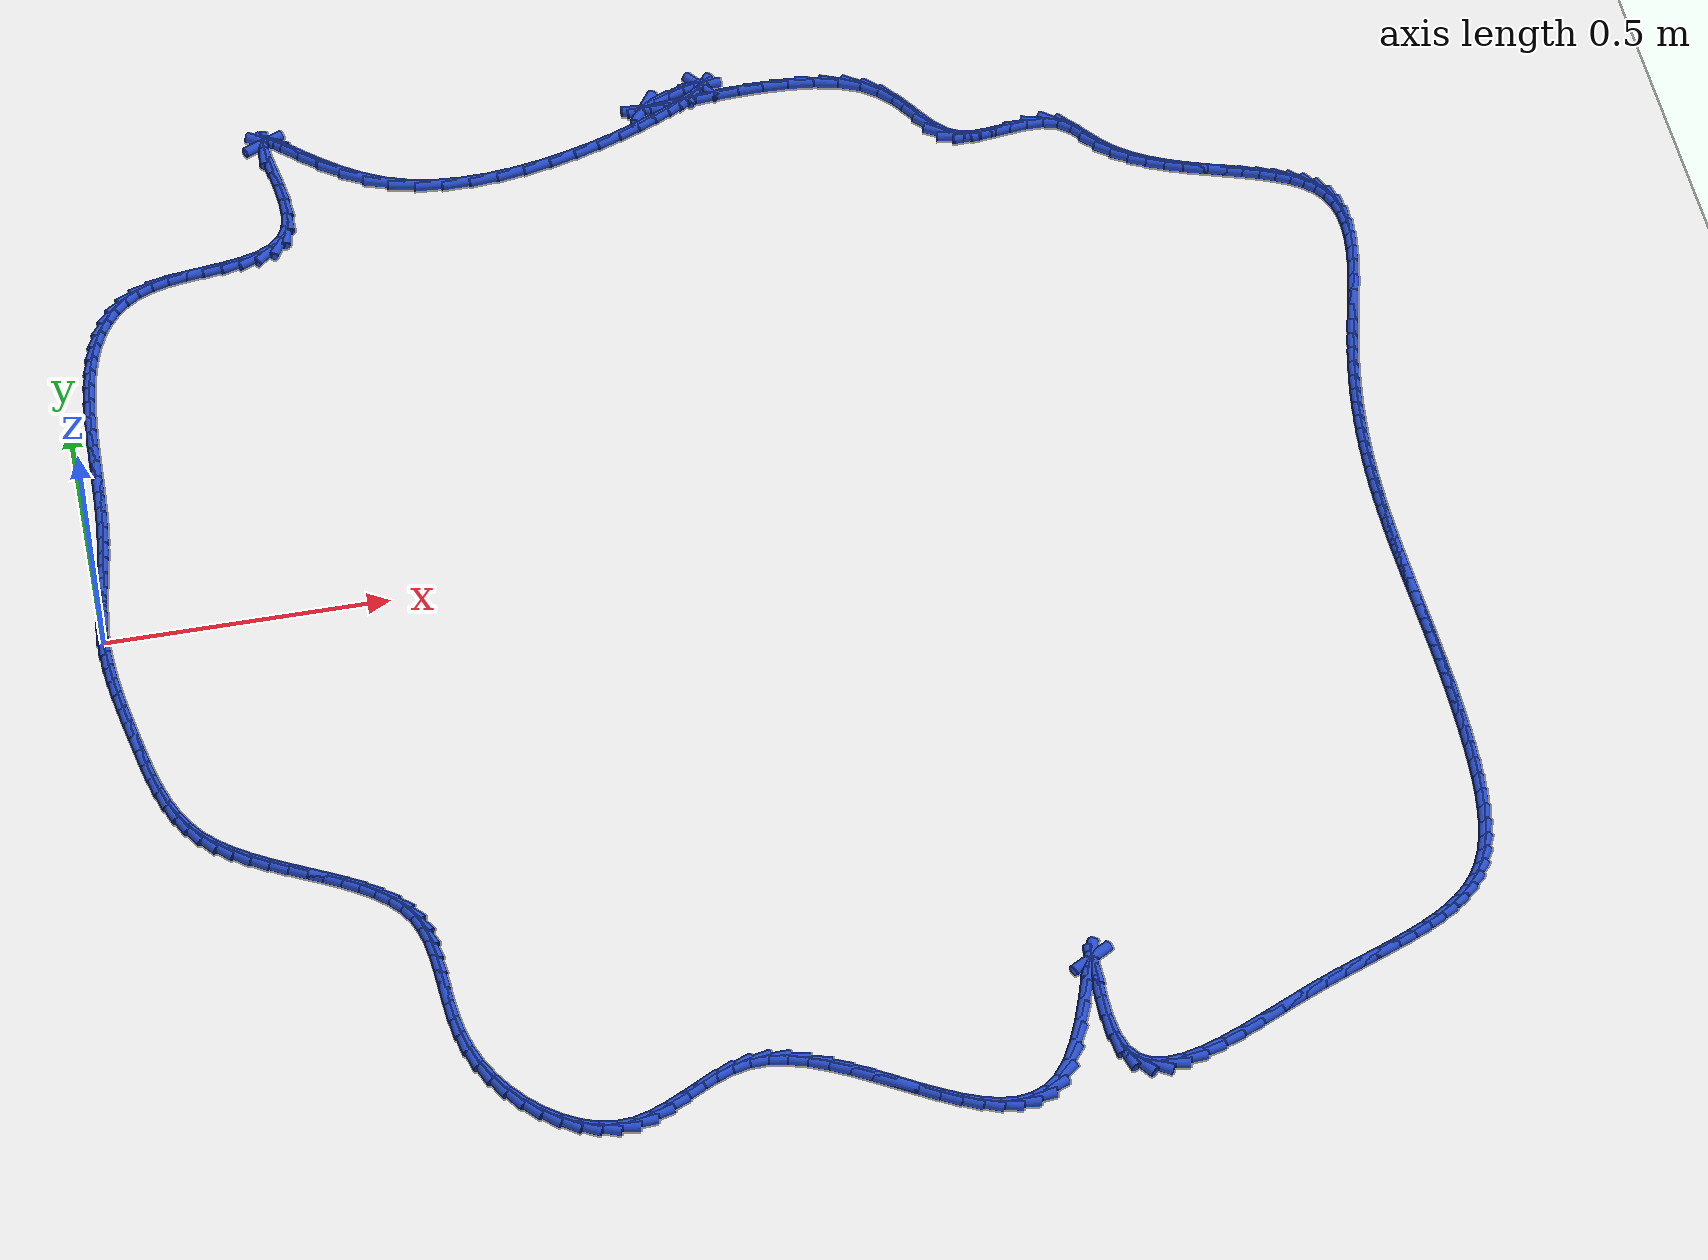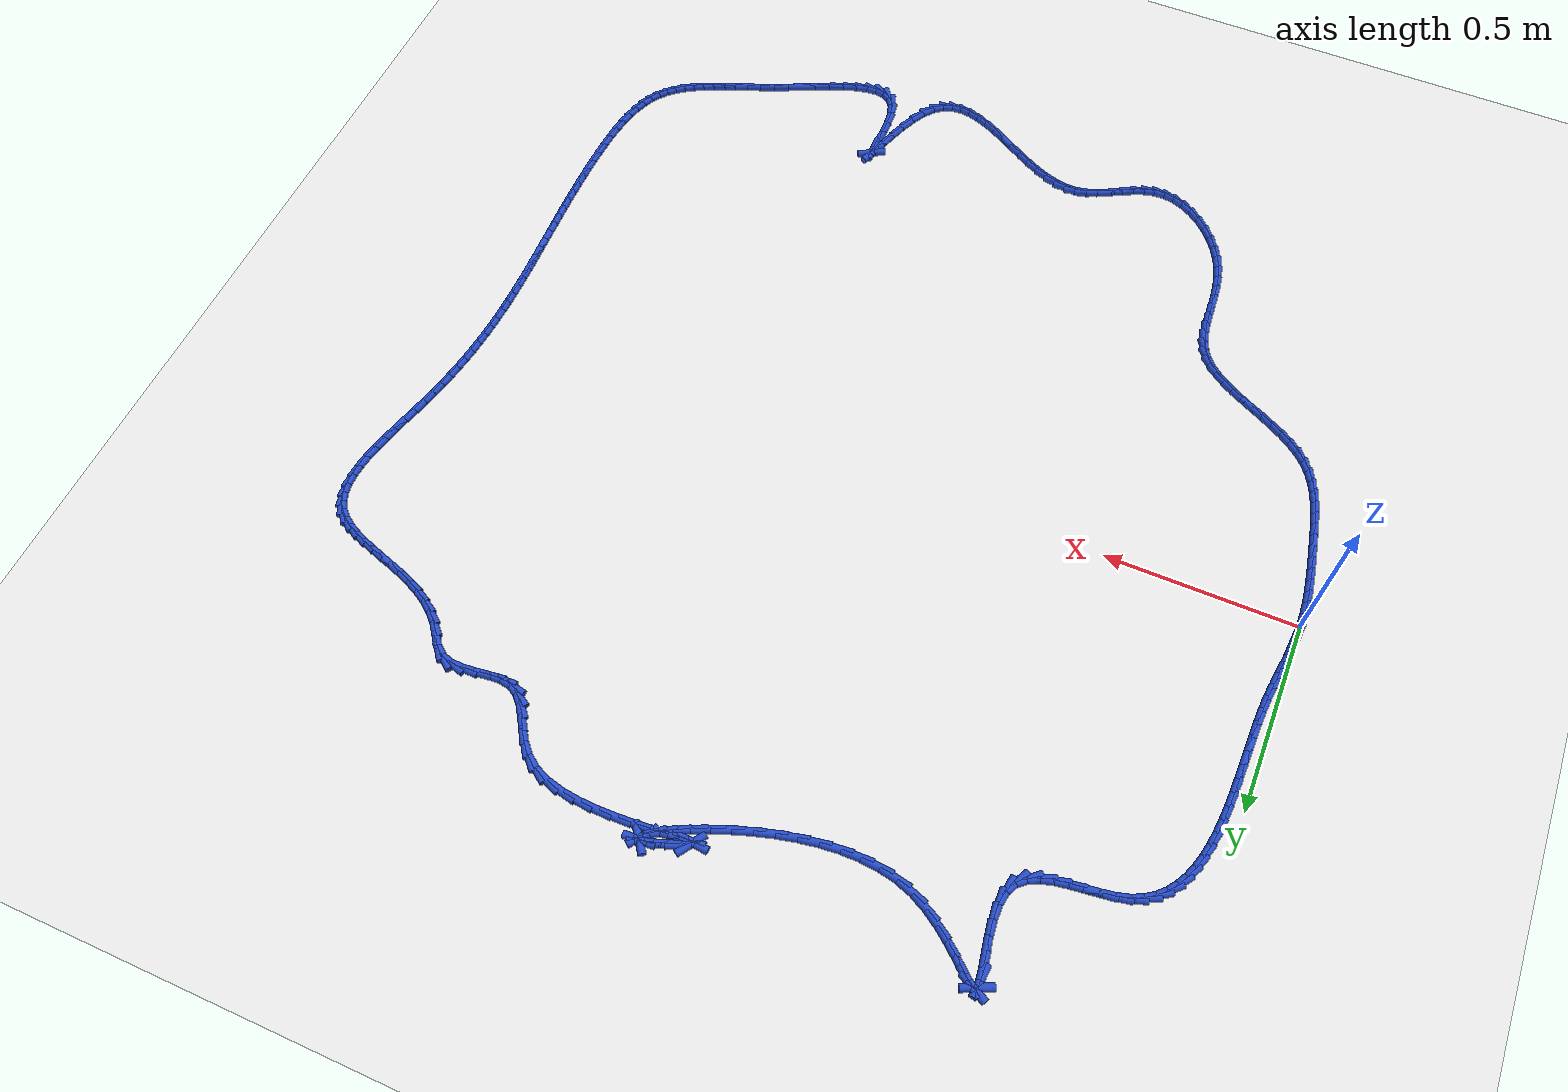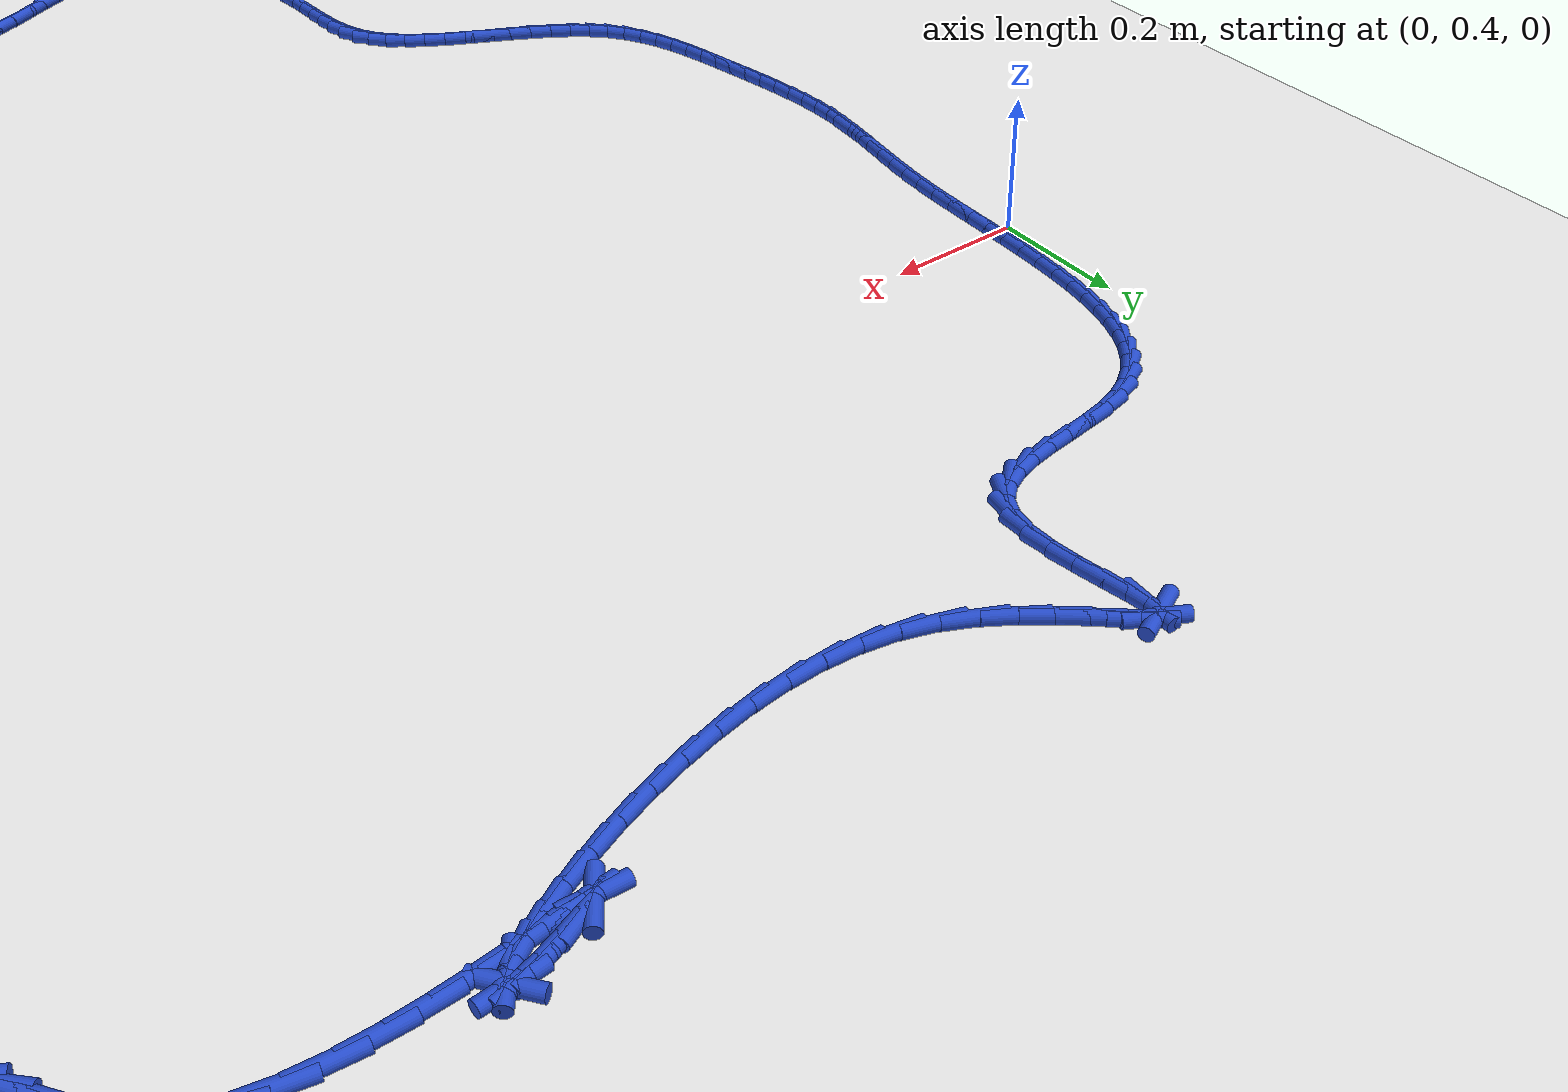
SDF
<sdf version="1.6">
 <world name="default">
  <light name="sun" type="directional">
   <pose>0 0 10 0 -0 0</pose>
   <diffuse>0.8 0.8 0.8 1</diffuse>
   <specular>0.2 0.2 0.2 1</specular>
   <attenuation>
    <range>1000</range>
    <constant>0.9</constant>
    <linear>0.01</linear>
    <quadratic>0.001</quadratic>
   </attenuation>
   <direction>-0.5 0.1 -0.9</direction>
  </light>
  <model name="ground_plane">
   <static>1</static>
   <link name="link">
    <collision name="collision">
     <geometry><plane><normal>0 0 1</normal><size>100 100</size></plane></geometry>
     <surface><friction><ode><mu>100</mu><mu2>50</mu2></ode></friction></surface>
    </collision>
    <visual name="visual">
     <cast_shadows>0</cast_shadows>
     <geometry><plane><normal>0 0 1</normal><size>100 100</size></plane></geometry>
     <material>
      <script><uri>file://media/materials/scripts/gazebo.material</uri><name>Gazebo/WhiteGlow</name></script>
     </material>
    </visual>
   </link>
  </model>
  <gravity>0 0 -9.8</gravity>
  <magnetic_field>6e-06 2.3e-05 -4.2e-05</magnetic_field>
  <atmosphere type="adiabatic"/>
  <physics name="default_physics" default="0" type="ode">
   <max_step_size>0.001</max_step_size>
   <real_time_factor>1</real_time_factor>
   <real_time_update_rate>1000</real_time_update_rate>
  </physics>
  <scene><ambient>0.4 0.4 0.4 1</ambient><background>0.7 0.7 0.7 1</background><shadows>1</shadows></scene>
  <spherical_coordinates>
   <surface_model>EARTH_WGS84</surface_model>
   <latitude_deg>0</latitude_deg>
   <longitude_deg>0</longitude_deg>
   <elevation>0</elevation>
   <heading_deg>0</heading_deg>
  </spherical_coordinates>
  <model name="line">
   <link name="link_0">
    <pose>-4.336808689942018e-18 2.7755575615628914e-17 0.01 0 1.57 1.5202288980639533</pose>
    <collision name="collision">
     <geometry><cylinder><radius>0.01</radius><length>0.08</length></cylinder></geometry>
    </collision>
    <visual name="visual">
     <material>
      <script><name>Gazebo/Blue</name><uri>file://media/materials/scripts/gazebo.material</uri></script>
     </material>
     <geometry><cylinder><radius>0.01</radius><length>0.08</length></cylinder></geometry>
    </visual>
   </link>
   <link name="link_1">
    <pose>0.0015129040999605175 0.029893043540428432 0.01 0 1.57 1.4756453663990243</pose>
    <collision name="collision">
     <geometry><cylinder><radius>0.01</radius><length>0.08</length></cylinder></geometry>
    </collision>
    <visual name="visual">
     <material>
      <script><name>Gazebo/Blue</name><uri>file://media/materials/scripts/gazebo.material</uri></script>
     </material>
     <geometry><cylinder><radius>0.01</radius><length>0.08</length></cylinder></geometry>
    </visual>
   </link>
   <link name="link_2">
    <pose>0.004360388436772055 0.05972864063501424 0.01 0 1.57 1.444542633726316</pose>
    <collision name="collision">
     <geometry><cylinder><radius>0.01</radius><length>0.08</length></cylinder></geometry>
    </collision>
    <visual name="visual">
     <material>
      <script><name>Gazebo/Blue</name><uri>file://media/materials/scripts/gazebo.material</uri></script>
     </material>
     <geometry><cylinder><radius>0.01</radius><length>0.08</length></cylinder></geometry>
    </visual>
   </link>
   <link name="link_3">
    <pose>0.008167238286608368 0.08972064462820215 0.01 0 1.57 1.4271717780435933</pose>
    <collision name="collision">
     <geometry><cylinder><radius>0.01</radius><length>0.08</length></cylinder></geometry>
    </collision>
    <visual name="visual">
     <material>
      <script><name>Gazebo/Blue</name><uri>file://media/materials/scripts/gazebo.material</uri></script>
     </material>
     <geometry><cylinder><radius>0.01</radius><length>0.08</length></cylinder></geometry>
    </visual>
   </link>
   <link name="link_4">
    <pose>0.012558238925643204 0.12008290886443686 0.01 0 1.57 1.4232345956230243</pose>
    <collision name="collision">
     <geometry><cylinder><radius>0.01</radius><length>0.08</length></cylinder></geometry>
    </collision>
    <visual name="visual">
     <material>
      <script><name>Gazebo/Blue</name><uri>file://media/materials/scripts/gazebo.material</uri></script>
     </material>
     <geometry><cylinder><radius>0.01</radius><length>0.08</length></cylinder></geometry>
    </visual>
   </link>
   <link name="link_5">
    <pose>0.017158175630050312 0.15102928668816304 0.01 0 1.57 1.4320263609322825</pose>
    <collision name="collision">
     <geometry><cylinder><radius>0.01</radius><length>0.08</length></cylinder></geometry>
    </collision>
    <visual name="visual">
     <material>
      <script><name>Gazebo/Blue</name><uri>file://media/materials/scripts/gazebo.material</uri></script>
     </material>
     <geometry><cylinder><radius>0.01</radius><length>0.08</length></cylinder></geometry>
    </visual>
   </link>
   <link name="link_6">
    <pose>0.021591833676003463 0.18277363144382552 0.01 0 1.57 1.4525284898363768</pose>
    <collision name="collision">
     <geometry><cylinder><radius>0.01</radius><length>0.08</length></cylinder></geometry>
    </collision>
    <visual name="visual">
     <material>
      <script><name>Gazebo/Blue</name><uri>file://media/materials/scripts/gazebo.material</uri></script>
     </material>
     <geometry><cylinder><radius>0.01</radius><length>0.08</length></cylinder></geometry>
    </visual>
   </link>
   <link name="link_7">
    <pose>0.025483998339676395 0.21552979647586884 0.01 0 1.57 1.48289890299912</pose>
    <collision name="collision">
     <geometry><cylinder><radius>0.01</radius><length>0.08</length></cylinder></geometry>
    </collision>
    <visual name="visual">
     <material>
      <script><name>Gazebo/Blue</name><uri>file://media/materials/scripts/gazebo.material</uri></script>
     </material>
     <geometry><cylinder><radius>0.01</radius><length>0.08</length></cylinder></geometry>
    </visual>
   </link>
   <link name="link_8">
    <pose>0.028477421534843825 0.24949791605129953 0.01 0 1.57 1.5120531029433644</pose>
    <collision name="collision">
     <geometry><cylinder><radius>0.01</radius><length>0.08</length></cylinder></geometry>
    </collision>
    <visual name="visual">
     <material>
      <script><name>Gazebo/Blue</name><uri>file://media/materials/scripts/gazebo.material</uri></script>
     </material>
     <geometry><cylinder><radius>0.01</radius><length>0.08</length></cylinder></geometry>
    </visual>
   </link>
   <link name="link_9">
    <pose>0.03054340856325931 0.28462724558753594 0.01 0 1.57 1.5320240932115652</pose>
    <collision name="collision">
     <geometry><cylinder><radius>0.01</radius><length>0.08</length></cylinder></geometry>
    </collision>
    <visual name="visual">
     <material>
      <script><name>Gazebo/Blue</name><uri>file://media/materials/scripts/gazebo.material</uri></script>
     </material>
     <geometry><cylinder><radius>0.01</radius><length>0.08</length></cylinder></geometry>
    </visual>
   </link>
   <link name="link_10">
    <pose>0.031940696900608 0.32064756124605476 0.01 0 1.57 1.543587007439992</pose>
    <collision name="collision">
     <geometry><cylinder><radius>0.01</radius><length>0.08</length></cylinder></geometry>
    </collision>
    <visual name="visual">
     <material>
      <script><name>Gazebo/Blue</name><uri>file://media/materials/scripts/gazebo.material</uri></script>
     </material>
     <geometry><cylinder><radius>0.01</radius><length>0.08</length></cylinder></geometry>
    </visual>
   </link>
   <link name="link_11">
    <pose>0.03293772029558363 0.35728123524758354 0.01 0 1.57 1.547397672989311</pose>
    <collision name="collision">
     <geometry><cylinder><radius>0.01</radius><length>0.08</length></cylinder></geometry>
    </collision>
    <visual name="visual">
     <material>
      <script><name>Gazebo/Blue</name><uri>file://media/materials/scripts/gazebo.material</uri></script>
     </material>
     <geometry><cylinder><radius>0.01</radius><length>0.08</length></cylinder></geometry>
    </visual>
   </link>
   <link name="link_12">
    <pose>0.033802912496879944 0.3942506398128497 0.01 0 1.57 1.543747505559048</pose>
    <collision name="collision">
     <geometry><cylinder><radius>0.01</radius><length>0.08</length></cylinder></geometry>
    </collision>
    <visual name="visual">
     <material>
      <script><name>Gazebo/Blue</name><uri>file://media/materials/scripts/gazebo.material</uri></script>
     </material>
     <geometry><cylinder><radius>0.01</radius><length>0.08</length></cylinder></geometry>
    </visual>
   </link>
   <link name="link_13">
    <pose>0.03480470725319068 0.4312781471625806 0.01 0 1.57 1.5325941075325964</pose>
    <collision name="collision">
     <geometry><cylinder><radius>0.01</radius><length>0.08</length></cylinder></geometry>
    </collision>
    <visual name="visual">
     <material>
      <script><name>Gazebo/Blue</name><uri>file://media/materials/scripts/gazebo.material</uri></script>
     </material>
     <geometry><cylinder><radius>0.01</radius><length>0.08</length></cylinder></geometry>
    </visual>
   </link>
   <link name="link_14">
    <pose>0.03621153831320953 0.46808612951750345 0.01 0 1.57 1.513567407996557</pose>
    <collision name="collision">
     <geometry><cylinder><radius>0.01</radius><length>0.08</length></cylinder></geometry>
    </collision>
    <visual name="visual">
     <material>
      <script><name>Gazebo/Blue</name><uri>file://media/materials/scripts/gazebo.material</uri></script>
     </material>
     <geometry><cylinder><radius>0.01</radius><length>0.08</length></cylinder></geometry>
    </visual>
   </link>
   <link name="link_15">
    <pose>0.03829183942563027 0.5043969590983457 0.01 0 1.57 1.485954312328354</pose>
    <collision name="collision">
     <geometry><cylinder><radius>0.01</radius><length>0.08</length></cylinder></geometry>
    </collision>
    <visual name="visual">
     <material>
      <script><name>Gazebo/Blue</name><uri>file://media/materials/scripts/gazebo.material</uri></script>
     </material>
     <geometry><cylinder><radius>0.01</radius><length>0.08</length></cylinder></geometry>
    </visual>
   </link>
   <link name="link_16">
    <pose>0.041314044339146594 0.5399330081258348 0.01 0 1.57 1.4486665955391353</pose>
    <collision name="collision">
     <geometry><cylinder><radius>0.01</radius><length>0.08</length></cylinder></geometry>
    </collision>
    <visual name="visual">
     <material>
      <script><name>Gazebo/Blue</name><uri>file://media/materials/scripts/gazebo.material</uri></script>
     </material>
     <geometry><cylinder><radius>0.01</radius><length>0.08</length></cylinder></geometry>
    </visual>
   </link>
   <link name="link_17">
    <pose>0.04554658680245226 0.5744166488206981 0.01 0 1.57 1.4002024509286566</pose>
    <collision name="collision">
     <geometry><cylinder><radius>0.01</radius><length>0.08</length></cylinder></geometry>
    </collision>
    <visual name="visual">
     <material>
      <script><name>Gazebo/Blue</name><uri>file://media/materials/scripts/gazebo.material</uri></script>
     </material>
     <geometry><cylinder><radius>0.01</radius><length>0.08</length></cylinder></geometry>
    </visual>
   </link>
   <link name="link_18">
    <pose>0.051257900564240955 0.6075702534036629 0.01 0 1.57 1.3386262734749519</pose>
    <collision name="collision">
     <geometry><cylinder><radius>0.01</radius><length>0.08</length></cylinder></geometry>
    </collision>
    <visual name="visual">
     <material>
      <script><name>Gazebo/Blue</name><uri>file://media/materials/scripts/gazebo.material</uri></script>
     </material>
     <geometry><cylinder><radius>0.01</radius><length>0.08</length></cylinder></geometry>
    </visual>
   </link>
   <link name="link_19">
    <pose>0.058716419373206465 0.6391161940954565 0.01 0 1.57 1.2616210306121727</pose>
    <collision name="collision">
     <geometry><cylinder><radius>0.01</radius><length>0.08</length></cylinder></geometry>
    </collision>
    <visual name="visual">
     <material>
      <script><name>Gazebo/Blue</name><uri>file://media/materials/scripts/gazebo.material</uri></script>
     </material>
     <geometry><cylinder><radius>0.01</radius><length>0.08</length></cylinder></geometry>
    </visual>
   </link>
   <link name="link_20">
    <pose>0.06819057697804247 0.6687768431168065 0.01 0 1.57 1.1667193394554887</pose>
    <collision name="collision">
     <geometry><cylinder><radius>0.01</radius><length>0.08</length></cylinder></geometry>
    </collision>
    <visual name="visual">
     <material>
      <script><name>Gazebo/Blue</name><uri>file://media/materials/scripts/gazebo.material</uri></script>
     </material>
     <geometry><cylinder><radius>0.01</radius><length>0.08</length></cylinder></geometry>
    </visual>
   </link>
   <link name="link_21">
    <pose>0.07994880712744273 0.69627457268844 0.01 0 1.57 1.0518804976627412</pose>
    <collision name="collision">
     <geometry><cylinder><radius>0.01</radius><length>0.08</length></cylinder></geometry>
    </collision>
    <visual name="visual">
     <material>
      <script><name>Gazebo/Blue</name><uri>file://media/materials/scripts/gazebo.material</uri></script>
     </material>
     <geometry><cylinder><radius>0.01</radius><length>0.08</length></cylinder></geometry>
    </visual>
   </link>
   <link name="link_22">
    <pose>0.09425954357010101 0.7213317550310847 0.01 0 1.57 0.9165697139929242</pose>
    <collision name="collision">
     <geometry><cylinder><radius>0.01</radius><length>0.08</length></cylinder></geometry>
    </collision>
    <visual name="visual">
     <material>
      <script><name>Gazebo/Blue</name><uri>file://media/materials/scripts/gazebo.material</uri></script>
     </material>
     <geometry><cylinder><radius>0.01</radius><length>0.08</length></cylinder></geometry>
    </visual>
   </link>
   <link name="link_23">
    <pose>0.11139122005471093 0.7436707623654676 0.01 0 1.57 0.763213953933341</pose>
    <collision name="collision">
     <geometry><cylinder><radius>0.01</radius><length>0.08</length></cylinder></geometry>
    </collision>
    <visual name="visual">
     <material>
      <script><name>Gazebo/Blue</name><uri>file://media/materials/scripts/gazebo.material</uri></script>
     </material>
     <geometry><cylinder><radius>0.01</radius><length>0.08</length></cylinder></geometry>
    </visual>
   </link>
   <link name="link_24">
    <pose>0.13161227032996634 0.7630139669123164 0.01 0 1.57 0.598224311668231</pose>
    <collision name="collision">
     <geometry><cylinder><radius>0.01</radius><length>0.08</length></cylinder></geometry>
    </collision>
    <visual name="visual">
     <material>
      <script><name>Gazebo/Blue</name><uri>file://media/materials/scripts/gazebo.material</uri></script>
     </material>
     <geometry><cylinder><radius>0.01</radius><length>0.08</length></cylinder></geometry>
    </visual>
   </link>
   <link name="link_25">
    <pose>0.15519112814456099 0.7790837408923583 0.01 0 1.57 0.43127131217248316</pose>
    <collision name="collision">
     <geometry><cylinder><radius>0.01</radius><length>0.08</length></cylinder></geometry>
    </collision>
    <visual name="visual">
     <material>
      <script><name>Gazebo/Blue</name><uri>file://media/materials/scripts/gazebo.material</uri></script>
     </material>
     <geometry><cylinder><radius>0.01</radius><length>0.08</length></cylinder></geometry>
    </visual>
   </link>
   <link name="link_26">
    <pose>0.18239622724718832 0.7916024565263204 0.01 0 1.57 0.27638062341504416</pose>
    <collision name="collision">
     <geometry><cylinder><radius>0.01</radius><length>0.08</length></cylinder></geometry>
    </collision>
    <visual name="visual">
     <material>
      <script><name>Gazebo/Blue</name><uri>file://media/materials/scripts/gazebo.material</uri></script>
     </material>
     <geometry><cylinder><radius>0.01</radius><length>0.08</length></cylinder></geometry>
    </visual>
   </link>
   <link name="link_27">
    <pose>0.21339208726880013 0.8003941138655105 0.01 0 1.57 0.17221420535591028</pose>
    <collision name="collision">
     <geometry><cylinder><radius>0.01</radius><length>0.08</length></cylinder></geometry>
    </collision>
    <visual name="visual">
     <material>
      <script><name>Gazebo/Blue</name><uri>file://media/materials/scripts/gazebo.material</uri></script>
     </material>
     <geometry><cylinder><radius>0.01</radius><length>0.08</length></cylinder></geometry>
    </visual>
   </link>
   <link name="link_28">
    <pose>0.24730957408101964 0.8062936245814646 0.01 0 1.57 0.12434120389702073</pose>
    <collision name="collision">
     <geometry><cylinder><radius>0.01</radius><length>0.08</length></cylinder></geometry>
    </collision>
    <visual name="visual">
     <material>
      <script><name>Gazebo/Blue</name><uri>file://media/materials/scripts/gazebo.material</uri></script>
     </material>
     <geometry><cylinder><radius>0.01</radius><length>0.08</length></cylinder></geometry>
    </visual>
   </link>
   <link name="link_29">
    <pose>0.2826870991806359 0.8107153197176031 0.01 0 1.57 0.12279427348534303</pose>
    <collision name="collision">
     <geometry><cylinder><radius>0.01</radius><length>0.08</length></cylinder></geometry>
    </collision>
    <visual name="visual">
     <material>
      <script><name>Gazebo/Blue</name><uri>file://media/materials/scripts/gazebo.material</uri></script>
     </material>
     <geometry><cylinder><radius>0.01</radius><length>0.08</length></cylinder></geometry>
    </visual>
   </link>
   <link name="link_30">
    <pose>0.3180560626779988 0.8150803874413692 0.01 0 1.57 0.1674729885325822</pose>
    <collision name="collision">
     <geometry><cylinder><radius>0.01</radius><length>0.08</length></cylinder></geometry>
    </collision>
    <visual name="visual">
     <material>
      <script><name>Gazebo/Blue</name><uri>file://media/materials/scripts/gazebo.material</uri></script>
     </material>
     <geometry><cylinder><radius>0.01</radius><length>0.08</length></cylinder></geometry>
    </visual>
   </link>
   <link name="link_31">
    <pose>0.35194786468345846 0.8208100159202066 0.01 0 1.57 0.26852291199545897</pose>
    <collision name="collision">
     <geometry><cylinder><radius>0.01</radius><length>0.08</length></cylinder></geometry>
    </collision>
    <visual name="visual">
     <material>
      <script><name>Gazebo/Blue</name><uri>file://media/materials/scripts/gazebo.material</uri></script>
     </material>
     <geometry><cylinder><radius>0.01</radius><length>0.08</length></cylinder></geometry>
    </visual>
   </link>
   <link name="link_32">
    <pose>0.3828939053073651 0.8293253933215589 0.01 0 1.57 0.4471249925249048</pose>
    <collision name="collision">
     <geometry><cylinder><radius>0.01</radius><length>0.08</length></cylinder></geometry>
    </collision>
    <visual name="visual">
     <material>
      <script><name>Gazebo/Blue</name><uri>file://media/materials/scripts/gazebo.material</uri></script>
     </material>
     <geometry><cylinder><radius>0.01</radius><length>0.08</length></cylinder></geometry>
    </visual>
   </link>
   <link name="link_33">
    <pose>0.4094255846600687 0.8420477078128692 0.01 0 1.57 0.7265347541526008</pose>
    <collision name="collision">
     <geometry><cylinder><radius>0.01</radius><length>0.08</length></cylinder></geometry>
    </collision>
    <visual name="visual">
     <material>
      <script><name>Gazebo/Blue</name><uri>file://media/materials/scripts/gazebo.material</uri></script>
     </material>
     <geometry><cylinder><radius>0.01</radius><length>0.08</length></cylinder></geometry>
    </visual>
   </link>
   <link name="link_34">
    <pose>0.43007430285191917 0.8603981475615816 0.01 0 1.57 1.0880038774104452</pose>
    <collision name="collision">
     <geometry><cylinder><radius>0.01</radius><length>0.08</length></cylinder></geometry>
    </collision>
    <visual name="visual">
     <material>
      <script><name>Gazebo/Blue</name><uri>file://media/materials/scripts/gazebo.material</uri></script>
     </material>
     <geometry><cylinder><radius>0.01</radius><length>0.08</length></cylinder></geometry>
    </visual>
   </link>
   <link name="link_35">
    <pose>0.4433814949817677 0.885785542589817 0.01 0 1.57 1.398865195183392</pose>
    <collision name="collision">
     <geometry><cylinder><radius>0.01</radius><length>0.08</length></cylinder></geometry>
    </collision>
    <visual name="visual">
     <material>
      <script><name>Gazebo/Blue</name><uri>file://media/materials/scripts/gazebo.material</uri></script>
     </material>
     <geometry><cylinder><radius>0.01</radius><length>0.08</length></cylinder></geometry>
    </visual>
   </link>
   <link name="link_36">
    <pose>0.44901549329827745 0.9182309426807157 0.01 0 1.57 -1.564622373786883</pose>
    <collision name="collision">
     <geometry><cylinder><radius>0.01</radius><length>0.08</length></cylinder></geometry>
    </collision>
    <visual name="visual">
     <material>
      <script><name>Gazebo/Blue</name><uri>file://media/materials/scripts/gazebo.material</uri></script>
     </material>
     <geometry><cylinder><radius>0.01</radius><length>0.08</length></cylinder></geometry>
    </visual>
   </link>
   <link name="link_37">
    <pose>0.4487877630709946 0.9551161171326 0.01 0 1.57 -1.4660555701461704</pose>
    <collision name="collision">
     <geometry><cylinder><radius>0.01</radius><length>0.08</length></cylinder></geometry>
    </collision>
    <visual name="visual">
     <material>
      <script><name>Gazebo/Blue</name><uri>file://media/materials/scripts/gazebo.material</uri></script>
     </material>
     <geometry><cylinder><radius>0.01</radius><length>0.08</length></cylinder></geometry>
    </visual>
   </link>
   <link name="link_38">
    <pose>0.4447497726015449 0.9935272701469506 0.01 0 1.57 -1.4154862054456478</pose>
    <collision name="collision">
     <geometry><cylinder><radius>0.01</radius><length>0.08</length></cylinder></geometry>
    </collision>
    <visual name="visual">
     <material>
      <script><name>Gazebo/Blue</name><uri>file://media/materials/scripts/gazebo.material</uri></script>
     </material>
     <geometry><cylinder><radius>0.01</radius><length>0.08</length></cylinder></geometry>
    </visual>
   </link>
   <link name="link_39">
    <pose>0.4389529901915544 1.0305506059252485 0.01 0 1.57 -1.4041468484341566</pose>
    <collision name="collision">
     <geometry><cylinder><radius>0.01</radius><length>0.08</length></cylinder></geometry>
    </collision>
    <visual name="visual">
     <material>
      <script><name>Gazebo/Blue</name><uri>file://media/materials/scripts/gazebo.material</uri></script>
     </material>
     <geometry><cylinder><radius>0.01</radius><length>0.08</length></cylinder></geometry>
    </visual>
   </link>
   <link name="link_40">
    <pose>0.43344888414264904 1.0632723286689738 0.01 0 1.57 -1.447535016017089</pose>
    <collision name="collision">
     <geometry><cylinder><radius>0.01</radius><length>0.08</length></cylinder></geometry>
    </collision>
    <visual name="visual">
     <material>
      <script><name>Gazebo/Blue</name><uri>file://media/materials/scripts/gazebo.material</uri></script>
     </material>
     <geometry><cylinder><radius>0.01</radius><length>0.08</length></cylinder></geometry>
    </visual>
   </link>
   <link name="link_41">
    <pose>0.4302889227564543 1.0887786425796073 0.01 0 1.57 1.4906122280855019</pose>
    <collision name="collision">
     <geometry><cylinder><radius>0.01</radius><length>0.08</length></cylinder></geometry>
    </collision>
    <visual name="visual">
     <material>
      <script><name>Gazebo/Blue</name><uri>file://media/materials/scripts/gazebo.material</uri></script>
     </material>
     <geometry><cylinder><radius>0.01</radius><length>0.08</length></cylinder></geometry>
    </visual>
   </link>
   <link name="link_42">
    <pose>0.43152457212432804 1.1041557566662041 0.01 0 1.57 0.4227158396568619</pose>
    <collision name="collision">
     <geometry><cylinder><radius>0.01</radius><length>0.08</length></cylinder></geometry>
    </collision>
    <visual name="visual">
     <material>
      <script><name>Gazebo/Blue</name><uri>file://media/materials/scripts/gazebo.material</uri></script>
     </material>
     <geometry><cylinder><radius>0.01</radius><length>0.08</length></cylinder></geometry>
    </visual>
   </link>
   <link name="link_43">
    <pose>0.43877992605209093 1.107419461264373 0.01 0 1.57 -0.5030792888731542</pose>
    <collision name="collision">
     <geometry><cylinder><radius>0.01</radius><length>0.08</length></cylinder></geometry>
    </collision>
    <visual name="visual">
     <material>
      <script><name>Gazebo/Blue</name><uri>file://media/materials/scripts/gazebo.material</uri></script>
     </material>
     <geometry><cylinder><radius>0.01</radius><length>0.08</length></cylinder></geometry>
    </visual>
   </link>
   <link name="link_44">
    <pose>0.45205746561134585 1.100112731245654 0.01 0 1.57 -0.6863518998554949</pose>
    <collision name="collision">
     <geometry><cylinder><radius>0.01</radius><length>0.08</length></cylinder></geometry>
    </collision>
    <visual name="visual">
     <material>
      <script><name>Gazebo/Blue</name><uri>file://media/materials/scripts/gazebo.material</uri></script>
     </material>
     <geometry><cylinder><radius>0.01</radius><length>0.08</length></cylinder></geometry>
    </visual>
   </link>
   <link name="link_45">
    <pose>0.47097511954146076 1.0846149847401365 0.01 0 1.57 -0.7224639154252251</pose>
    <collision name="collision">
     <geometry><cylinder><radius>0.01</radius><length>0.08</length></cylinder></geometry>
    </collision>
    <visual name="visual">
     <material>
      <script><name>Gazebo/Blue</name><uri>file://media/materials/scripts/gazebo.material</uri></script>
     </material>
     <geometry><cylinder><radius>0.01</radius><length>0.08</length></cylinder></geometry>
    </visual>
   </link>
   <link name="link_46">
    <pose>0.4951508165818031 1.0633056398779106 0.01 0 1.57 -0.7054446363264925</pose>
    <collision name="collision">
     <geometry><cylinder><radius>0.01</radius><length>0.08</length></cylinder></geometry>
    </collision>
    <visual name="visual">
     <material>
      <script><name>Gazebo/Blue</name><uri>file://media/materials/scripts/gazebo.material</uri></script>
     </material>
     <geometry><cylinder><radius>0.01</radius><length>0.08</length></cylinder></geometry>
    </visual>
   </link>
   <link name="link_47">
    <pose>0.5242024854717409 1.0385641147890652 0.01 0 1.57 -0.6555083715265565</pose>
    <collision name="collision">
     <geometry><cylinder><radius>0.01</radius><length>0.08</length></cylinder></geometry>
    </collision>
    <visual name="visual">
     <material>
      <script><name>Gazebo/Blue</name><uri>file://media/materials/scripts/gazebo.material</uri></script>
     </material>
     <geometry><cylinder><radius>0.01</radius><length>0.08</length></cylinder></geometry>
    </visual>
   </link>
   <link name="link_48">
    <pose>0.557748054950642 1.0127698276036905 0.01 0 1.57 -0.5761945292690872</pose>
    <collision name="collision">
     <geometry><cylinder><radius>0.01</radius><length>0.08</length></cylinder></geometry>
    </collision>
    <visual name="visual">
     <material>
      <script><name>Gazebo/Blue</name><uri>file://media/materials/scripts/gazebo.material</uri></script>
     </material>
     <geometry><cylinder><radius>0.01</radius><length>0.08</length></cylinder></geometry>
    </visual>
   </link>
   <link name="link_49">
    <pose>0.5954054537578741 0.988302196451876 0.01 0 1.57 -0.46496074832424406</pose>
    <collision name="collision">
     <geometry><cylinder><radius>0.01</radius><length>0.08</length></cylinder></geometry>
    </collision>
    <visual name="visual">
     <material>
      <script><name>Gazebo/Blue</name><uri>file://media/materials/scripts/gazebo.material</uri></script>
     </material>
     <geometry><cylinder><radius>0.01</radius><length>0.08</length></cylinder></geometry>
    </visual>
   </link>
   <link name="link_50">
    <pose>0.6367926106328052 0.9675406394637116 0.01 0 1.57 -0.3218720947109697</pose>
    <collision name="collision">
     <geometry><cylinder><radius>0.01</radius><length>0.08</length></cylinder></geometry>
    </collision>
    <visual name="visual">
     <material>
      <script><name>Gazebo/Blue</name><uri>file://media/materials/scripts/gazebo.material</uri></script>
     </material>
     <geometry><cylinder><radius>0.01</radius><length>0.08</length></cylinder></geometry>
    </visual>
   </link>
   <link name="link_51">
    <pose>0.6814991036683175 0.9526324374947773 0.01 0 1.57 -0.18347761992087347</pose>
    <collision name="collision">
     <geometry><cylinder><radius>0.01</radius><length>0.08</length></cylinder></geometry>
    </collision>
    <visual name="visual">
     <material>
      <script><name>Gazebo/Blue</name><uri>file://media/materials/scripts/gazebo.material</uri></script>
     </material>
     <geometry><cylinder><radius>0.01</radius><length>0.08</length></cylinder></geometry>
    </visual>
   </link>
   <link name="link_52">
    <pose>0.7288842446442348 0.9438394331143486 0.01 0 1.57 -0.06747565027257112</pose>
    <collision name="collision">
     <geometry><cylinder><radius>0.01</radius><length>0.08</length></cylinder></geometry>
    </collision>
    <visual name="visual">
     <material>
      <script><name>Gazebo/Blue</name><uri>file://media/materials/scripts/gazebo.material</uri></script>
     </material>
     <geometry><cylinder><radius>0.01</radius><length>0.08</length></cylinder></geometry>
    </visual>
   </link>
   <link name="link_53">
    <pose>0.7781954266605198 0.940507070130811 0.01 0 1.57 0.029063087903408547</pose>
    <collision name="collision">
     <geometry><cylinder><radius>0.01</radius><length>0.08</length></cylinder></geometry>
    </collision>
    <visual name="visual">
     <material>
      <script><name>Gazebo/Blue</name><uri>file://media/materials/scripts/gazebo.material</uri></script>
     </material>
     <geometry><cylinder><radius>0.01</radius><length>0.08</length></cylinder></geometry>
    </visual>
   </link>
   <link name="link_54">
    <pose>0.828679298837078 0.9419747005866063 0.01 0 1.57 0.10970748252721775</pose>
    <collision name="collision">
     <geometry><cylinder><radius>0.01</radius><length>0.08</length></cylinder></geometry>
    </collision>
    <visual name="visual">
     <material>
      <script><name>Gazebo/Blue</name><uri>file://media/materials/scripts/gazebo.material</uri></script>
     </material>
     <geometry><cylinder><radius>0.01</radius><length>0.08</length></cylinder></geometry>
    </visual>
   </link>
   <link name="link_55">
    <pose>0.8795825102938156 0.9475816765241765 0.01 0 1.57 0.17777146263162247</pose>
    <collision name="collision">
     <geometry><cylinder><radius>0.01</radius><length>0.08</length></cylinder></geometry>
    </collision>
    <visual name="visual">
     <material>
      <script><name>Gazebo/Blue</name><uri>file://media/materials/scripts/gazebo.material</uri></script>
     </material>
     <geometry><cylinder><radius>0.01</radius><length>0.08</length></cylinder></geometry>
    </visual>
   </link>
   <link name="link_56">
    <pose>0.9301517101506377 0.956667349985964 0.01 0 1.57 0.23608152516571862</pose>
    <collision name="collision">
     <geometry><cylinder><radius>0.01</radius><length>0.08</length></cylinder></geometry>
    </collision>
    <visual name="visual">
     <material>
      <script><name>Gazebo/Blue</name><uri>file://media/materials/scripts/gazebo.material</uri></script>
     </material>
     <geometry><cylinder><radius>0.01</radius><length>0.08</length></cylinder></geometry>
    </visual>
   </link>
   <link name="link_57">
    <pose>0.9796335475274502 0.9685710730144109 0.01 0 1.57 0.2869983788057512</pose>
    <collision name="collision">
     <geometry><cylinder><radius>0.01</radius><length>0.08</length></cylinder></geometry>
    </collision>
    <visual name="visual">
     <material>
      <script><name>Gazebo/Blue</name><uri>file://media/materials/scripts/gazebo.material</uri></script>
     </material>
     <geometry><cylinder><radius>0.01</radius><length>0.08</length></cylinder></geometry>
    </visual>
   </link>
   <link name="link_58">
    <pose>1.0272746715441594 0.9826321976519592 0.01 0 1.57 0.33254366720948786</pose>
    <collision name="collision">
     <geometry><cylinder><radius>0.01</radius><length>0.08</length></cylinder></geometry>
    </collision>
    <visual name="visual">
     <material>
      <script><name>Gazebo/Blue</name><uri>file://media/materials/scripts/gazebo.material</uri></script>
     </material>
     <geometry><cylinder><radius>0.01</radius><length>0.08</length></cylinder></geometry>
    </visual>
   </link>
   <link name="link_59">
    <pose>1.0723217313206703 0.9981900759410511 0.01 0 1.57 0.37458248785209297</pose>
    <collision name="collision">
     <geometry><cylinder><radius>0.01</radius><length>0.08</length></cylinder></geometry>
    </collision>
    <visual name="visual">
     <material>
      <script><name>Gazebo/Blue</name><uri>file://media/materials/scripts/gazebo.material</uri></script>
     </material>
     <geometry><cylinder><radius>0.01</radius><length>0.08</length></cylinder></geometry>
    </visual>
   </link>
   <link name="link_60">
    <pose>1.114021375976889 1.0145840599241283 0.01 0 1.57 0.41508462988960904</pose>
    <collision name="collision">
     <geometry><cylinder><radius>0.01</radius><length>0.08</length></cylinder></geometry>
    </collision>
    <visual name="visual">
     <material>
      <script><name>Gazebo/Blue</name><uri>file://media/materials/scripts/gazebo.material</uri></script>
     </material>
     <geometry><cylinder><radius>0.01</radius><length>0.08</length></cylinder></geometry>
    </visual>
   </link>
   <link name="link_61">
    <pose>1.1516202546327217 1.0311535016436337 0.01 0 1.57 0.45658346132957645</pose>
    <collision name="collision">
     <geometry><cylinder><radius>0.01</radius><length>0.08</length></cylinder></geometry>
    </collision>
    <visual name="visual">
     <material>
      <script><name>Gazebo/Blue</name><uri>file://media/materials/scripts/gazebo.material</uri></script>
     </material>
     <geometry><cylinder><radius>0.01</radius><length>0.08</length></cylinder></geometry>
    </visual>
   </link>
   <link name="link_62">
    <pose>1.184365016408073 1.0472377531420085 0.01 0 1.57 0.5032081433869521</pose>
    <collision name="collision">
     <geometry><cylinder><radius>0.01</radius><length>0.08</length></cylinder></geometry>
    </collision>
    <visual name="visual">
     <material>
      <script><name>Gazebo/Blue</name><uri>file://media/materials/scripts/gazebo.material</uri></script>
     </material>
     <geometry><cylinder><radius>0.01</radius><length>0.08</length></cylinder></geometry>
    </visual>
   </link>
   <link name="link_63">
    <pose>1.2115023104228497 1.0621761664616955 0.01 0 1.57 0.563658285069248</pose>
    <collision name="collision">
     <geometry><cylinder><radius>0.01</radius><length>0.08</length></cylinder></geometry>
    </collision>
    <visual name="visual">
     <material>
      <script><name>Gazebo/Blue</name><uri>file://media/materials/scripts/gazebo.material</uri></script>
     </material>
     <geometry><cylinder><radius>0.01</radius><length>0.08</length></cylinder></geometry>
    </visual>
   </link>
   <link name="link_64">
    <pose>1.2322787857969568 1.0753080936451365 0.01 0 1.57 0.6627990967826926</pose>
    <collision name="collision">
     <geometry><cylinder><radius>0.01</radius><length>0.08</length></cylinder></geometry>
    </collision>
    <visual name="visual">
     <material>
      <script><name>Gazebo/Blue</name><uri>file://media/materials/scripts/gazebo.material</uri></script>
     </material>
     <geometry><cylinder><radius>0.01</radius><length>0.08</length></cylinder></geometry>
    </visual>
   </link>
   <link name="link_65">
    <pose>1.2459410916503009 1.0859728867347738 0.01 0 1.57 0.9153437566889868</pose>
    <collision name="collision">
     <geometry><cylinder><radius>0.01</radius><length>0.08</length></cylinder></geometry>
    </collision>
    <visual name="visual">
     <material>
      <script><name>Gazebo/Blue</name><uri>file://media/materials/scripts/gazebo.material</uri></script>
     </material>
     <geometry><cylinder><radius>0.01</radius><length>0.08</length></cylinder></geometry>
    </visual>
   </link>
   <link name="link_66">
    <pose>1.2517358771027867 1.093509897773049 0.01 0 1.57 -0.9247986837453452</pose>
    <collision name="collision">
     <geometry><cylinder><radius>0.01</radius><length>0.08</length></cylinder></geometry>
    </collision>
    <visual name="visual">
     <material>
      <script><name>Gazebo/Blue</name><uri>file://media/materials/scripts/gazebo.material</uri></script>
     </material>
     <geometry><cylinder><radius>0.01</radius><length>0.08</length></cylinder></geometry>
    </visual>
   </link>
   <link name="link_67">
    <pose>1.2489097912743201 1.0972584788024045 0.01 0 1.57 0.05735336319084578</pose>
    <collision name="collision">
     <geometry><cylinder><radius>0.01</radius><length>0.08</length></cylinder></geometry>
    </collision>
    <visual name="visual">
     <material>
      <script><name>Gazebo/Blue</name><uri>file://media/materials/scripts/gazebo.material</uri></script>
     </material>
     <geometry><cylinder><radius>0.01</radius><length>0.08</length></cylinder></geometry>
    </visual>
   </link>
   <link name="link_68">
    <pose>1.2367094832848076 1.0965579818652826 0.01 0 1.57 0.2545740996486978</pose>
    <collision name="collision">
     <geometry><cylinder><radius>0.01</radius><length>0.08</length></cylinder></geometry>
    </collision>
    <visual name="visual">
     <material>
      <script><name>Gazebo/Blue</name><uri>file://media/materials/scripts/gazebo.material</uri></script>
     </material>
     <geometry><cylinder><radius>0.01</radius><length>0.08</length></cylinder></geometry>
    </visual>
   </link>
   <link name="link_69">
    <pose>1.214381984725351 1.0907479206085327 0.01 0 1.57 0.33034324934001646</pose>
    <collision name="collision">
     <geometry><cylinder><radius>0.01</radius><length>0.08</length></cylinder></geometry>
    </collision>
    <visual name="visual">
     <material>
      <script><name>Gazebo/Blue</name><uri>file://media/materials/scripts/gazebo.material</uri></script>
     </material>
     <geometry><cylinder><radius>0.01</radius><length>0.08</length></cylinder></geometry>
    </visual>
   </link>
   <link name="link_70">
    <pose>1.1835974568897007 1.0801916464040222 0.01 0 1.57 0.3724616160630466</pose>
    <collision name="collision">
     <geometry><cylinder><radius>0.01</radius><length>0.08</length></cylinder></geometry>
    </collision>
    <visual name="visual">
     <material>
      <script><name>Gazebo/Blue</name><uri>file://media/materials/scripts/gazebo.material</uri></script>
     </material>
     <geometry><cylinder><radius>0.01</radius><length>0.08</length></cylinder></geometry>
    </visual>
   </link>
   <link name="link_71">
    <pose>1.1541969793328282 1.068704944207645 0.01 0 1.57 0.44316154165610844</pose>
    <collision name="collision">
     <geometry><cylinder><radius>0.01</radius><length>0.08</length></cylinder></geometry>
    </collision>
    <visual name="visual">
     <material>
      <script><name>Gazebo/Blue</name><uri>file://media/materials/scripts/gazebo.material</uri></script>
     </material>
     <geometry><cylinder><radius>0.01</radius><length>0.08</length></cylinder></geometry>
    </visual>
   </link>
   <link name="link_72">
    <pose>1.1368426358532968 1.06046773032503 0.01 0 1.57 0.9736820072938392</pose>
    <collision name="collision">
     <geometry><cylinder><radius>0.01</radius><length>0.08</length></cylinder></geometry>
    </collision>
    <visual name="visual">
     <material>
      <script><name>Gazebo/Blue</name><uri>file://media/materials/scripts/gazebo.material</uri></script>
     </material>
     <geometry><cylinder><radius>0.01</radius><length>0.08</length></cylinder></geometry>
    </visual>
   </link>
   <link name="link_73">
    <pose>1.1340626772042415 1.0563790077112274 0.01 0 1.57 -0.07824138457204957</pose>
    <collision name="collision">
     <geometry><cylinder><radius>0.01</radius><length>0.08</length></cylinder></geometry>
    </collision>
    <visual name="visual">
     <material>
      <script><name>Gazebo/Blue</name><uri>file://media/materials/scripts/gazebo.material</uri></script>
     </material>
     <geometry><cylinder><radius>0.01</radius><length>0.08</length></cylinder></geometry>
    </visual>
   </link>
   <link name="link_74">
    <pose>1.1440644121384256 1.055594857353635 0.01 0 1.57 0.07908773419472392</pose>
    <collision name="collision">
     <geometry><cylinder><radius>0.01</radius><length>0.08</length></cylinder></geometry>
    </collision>
    <visual name="visual">
     <material>
      <script><name>Gazebo/Blue</name><uri>file://media/materials/scripts/gazebo.material</uri></script>
     </material>
     <geometry><cylinder><radius>0.01</radius><length>0.08</length></cylinder></geometry>
    </visual>
   </link>
   <link name="link_75">
    <pose>1.1650152772311972 1.0572552771508452 0.01 0 1.57 0.10750756838707232</pose>
    <collision name="collision">
     <geometry><cylinder><radius>0.01</radius><length>0.08</length></cylinder></geometry>
    </collision>
    <visual name="visual">
     <material>
      <script><name>Gazebo/Blue</name><uri>file://media/materials/scripts/gazebo.material</uri></script>
     </material>
     <geometry><cylinder><radius>0.01</radius><length>0.08</length></cylinder></geometry>
    </visual>
   </link>
   <link name="link_76">
    <pose>1.1950827090579046 1.06050026500145 0.01 0 1.57 0.10587838150922724</pose>
    <collision name="collision">
     <geometry><cylinder><radius>0.01</radius><length>0.08</length></cylinder></geometry>
    </collision>
    <visual name="visual">
     <material>
      <script><name>Gazebo/Blue</name><uri>file://media/materials/scripts/gazebo.material</uri></script>
     </material>
     <geometry><cylinder><radius>0.01</radius><length>0.08</length></cylinder></geometry>
    </visual>
   </link>
   <link name="link_77">
    <pose>1.2324341441938962 1.0644698188040418 0.01 0 1.57 0.0893377347609236</pose>
    <collision name="collision">
     <geometry><cylinder><radius>0.01</radius><length>0.08</length></cylinder></geometry>
    </collision>
    <visual name="visual">
     <material>
      <script><name>Gazebo/Blue</name><uri>file://media/materials/scripts/gazebo.material</uri></script>
     </material>
     <geometry><cylinder><radius>0.01</radius><length>0.08</length></cylinder></geometry>
    </visual>
   </link>
   <link name="link_78">
    <pose>1.2752370192145204 1.0683039364572133 0.01 0 1.57 0.061073721042350586</pose>
    <collision name="collision">
     <geometry><cylinder><radius>0.01</radius><length>0.08</length></cylinder></geometry>
    </collision>
    <visual name="visual">
     <material>
      <script><name>Gazebo/Blue</name><uri>file://media/materials/scripts/gazebo.material</uri></script>
     </material>
     <geometry><cylinder><radius>0.01</radius><length>0.08</length></cylinder></geometry>
    </visual>
   </link>
   <link name="link_79">
    <pose>1.3216587706951255 1.0711426158595567 0.01 0 1.57 0.0203929105236451</pose>
    <collision name="collision">
     <geometry><cylinder><radius>0.01</radius><length>0.08</length></cylinder></geometry>
    </collision>
    <visual name="visual">
     <material>
      <script><name>Gazebo/Blue</name><uri>file://media/materials/scripts/gazebo.material</uri></script>
     </material>
     <geometry><cylinder><radius>0.01</radius><length>0.08</length></cylinder></geometry>
    </visual>
   </link>
   <link name="link_80">
    <pose>1.3698668352110581 1.072125854909664 0.01 0 1.57 -0.035950827467834644</pose>
    <collision name="collision">
     <geometry><cylinder><radius>0.01</radius><length>0.08</length></cylinder></geometry>
    </collision>
    <visual name="visual">
     <material>
      <script><name>Gazebo/Blue</name><uri>file://media/materials/scripts/gazebo.material</uri></script>
     </material>
     <geometry><cylinder><radius>0.01</radius><length>0.08</length></cylinder></geometry>
    </visual>
   </link>
   <link name="link_81">
    <pose>1.4180286493376697 1.070393651506128 0.01 0 1.57 -0.11417934702417244</pose>
    <collision name="collision">
     <geometry><cylinder><radius>0.01</radius><length>0.08</length></cylinder></geometry>
    </collision>
    <visual name="visual">
     <material>
      <script><name>Gazebo/Blue</name><uri>file://media/materials/scripts/gazebo.material</uri></script>
     </material>
     <geometry><cylinder><radius>0.01</radius><length>0.08</length></cylinder></geometry>
    </visual>
   </link>
   <link name="link_82">
    <pose>1.4643116496503066 1.0650860035475411 0.01 0 1.57 -0.22498880895736634</pose>
    <collision name="collision">
     <geometry><cylinder><radius>0.01</radius><length>0.08</length></cylinder></geometry>
    </collision>
    <visual name="visual">
     <material>
      <script><name>Gazebo/Blue</name><uri>file://media/materials/scripts/gazebo.material</uri></script>
     </material>
     <geometry><cylinder><radius>0.01</radius><length>0.08</length></cylinder></geometry>
    </visual>
   </link>
   <link name="link_83">
    <pose>1.506883272724317 1.0553429089324953 0.01 0 1.57 -0.3857910404454256</pose>
    <collision name="collision">
     <geometry><cylinder><radius>0.01</radius><length>0.08</length></cylinder></geometry>
    </collision>
    <visual name="visual">
     <material>
      <script><name>Gazebo/Blue</name><uri>file://media/materials/scripts/gazebo.material</uri></script>
     </material>
     <geometry><cylinder><radius>0.01</radius><length>0.08</length></cylinder></geometry>
    </visual>
   </link>
   <link name="link_84">
    <pose>1.54391095513505 1.0403043655595832 0.01 0 1.57 -0.6079140005670933</pose>
    <collision name="collision">
     <geometry><cylinder><radius>0.01</radius><length>0.08</length></cylinder></geometry>
    </collision>
    <visual name="visual">
     <material>
      <script><name>Gazebo/Blue</name><uri>file://media/materials/scripts/gazebo.material</uri></script>
     </material>
     <geometry><cylinder><radius>0.01</radius><length>0.08</length></cylinder></geometry>
    </visual>
   </link>
   <link name="link_85">
    <pose>1.573930439409148 1.0194162562277398 0.01 0 1.57 -0.8117997148209194</pose>
    <collision name="collision">
     <geometry><cylinder><radius>0.01</radius><length>0.08</length></cylinder></geometry>
    </collision>
    <visual name="visual">
     <material>
      <script><name>Gazebo/Blue</name><uri>file://media/materials/scripts/gazebo.material</uri></script>
     </material>
     <geometry><cylinder><radius>0.01</radius><length>0.08</length></cylinder></geometry>
    </visual>
   </link>
   <link name="link_86">
    <pose>1.597905292503343 0.9941408168011628 0.01 0 1.57 -0.9429371162151671</pose>
    <collision name="collision">
     <geometry><cylinder><radius>0.01</radius><length>0.08</length></cylinder></geometry>
    </collision>
    <visual name="visual">
     <material>
      <script><name>Gazebo/Blue</name><uri>file://media/materials/scripts/gazebo.material</uri></script>
     </material>
     <geometry><cylinder><radius>0.01</radius><length>0.08</length></cylinder></geometry>
    </visual>
   </link>
   <link name="link_87">
    <pose>1.617781917832077 0.966756546988994 0.01 0 1.57 -0.9933990592748085</pose>
    <collision name="collision">
     <geometry><cylinder><radius>0.01</radius><length>0.08</length></cylinder></geometry>
    </collision>
    <visual name="visual">
     <material>
      <script><name>Gazebo/Blue</name><uri>file://media/materials/scripts/gazebo.material</uri></script>
     </material>
     <geometry><cylinder><radius>0.01</radius><length>0.08</length></cylinder></geometry>
    </visual>
   </link>
   <link name="link_88">
    <pose>1.6355094973933693 0.9395442541653972 0.01 0 1.57 -0.9547756335112859</pose>
    <collision name="collision">
     <geometry><cylinder><radius>0.01</radius><length>0.08</length></cylinder></geometry>
    </collision>
    <visual name="visual">
     <material>
      <script><name>Gazebo/Blue</name><uri>file://media/materials/scripts/gazebo.material</uri></script>
     </material>
     <geometry><cylinder><radius>0.01</radius><length>0.08</length></cylinder></geometry>
    </visual>
   </link>
   <link name="link_89">
    <pose>1.6530372131852389 0.9147847457045346 0.01 0 1.57 -0.804449966875273</pose>
    <collision name="collision">
     <geometry><cylinder><radius>0.01</radius><length>0.08</length></cylinder></geometry>
    </collision>
    <visual name="visual">
     <material>
      <script><name>Gazebo/Blue</name><uri>file://media/materials/scripts/gazebo.material</uri></script>
     </material>
     <geometry><cylinder><radius>0.01</radius><length>0.08</length></cylinder></geometry>
    </visual>
   </link>
   <link name="link_90">
    <pose>1.6723142472057069 0.8947588289805707 0.01 0 1.57 -0.5152869933899991</pose>
    <collision name="collision">
     <geometry><cylinder><radius>0.01</radius><length>0.08</length></cylinder></geometry>
    </collision>
    <visual name="visual">
     <material>
      <script><name>Gazebo/Blue</name><uri>file://media/materials/scripts/gazebo.material</uri></script>
     </material>
     <geometry><cylinder><radius>0.01</radius><length>0.08</length></cylinder></geometry>
    </visual>
   </link>
   <link name="link_91">
    <pose>1.6952897814527916 0.8817473113676679 0.01 0 1.57 -0.16192909802591032</pose>
    <collision name="collision">
     <geometry><cylinder><radius>0.01</radius><length>0.08</length></cylinder></geometry>
    </collision>
    <visual name="visual">
     <material>
      <script><name>Gazebo/Blue</name><uri>file://media/materials/scripts/gazebo.material</uri></script>
     </material>
     <geometry><cylinder><radius>0.01</radius><length>0.08</length></cylinder></geometry>
    </visual>
   </link>
   <link name="link_92">
    <pose>1.7233233265135468 0.8771677677691238 0.01 0 1.57 0.04747561229783782</pose>
    <collision name="collision">
     <geometry><cylinder><radius>0.01</radius><length>0.08</length></cylinder></geometry>
    </collision>
    <visual name="visual">
     <material>
      <script><name>Gazebo/Blue</name><uri>file://media/materials/scripts/gazebo.material</uri></script>
     </material>
     <geometry><cylinder><radius>0.01</radius><length>0.08</length></cylinder></geometry>
    </visual>
   </link>
   <link name="link_93">
    <pose>1.7552093233760797 0.8786827133606366 0.01 0 1.57 0.12498669931992888</pose>
    <collision name="collision">
     <geometry><cylinder><radius>0.01</radius><length>0.08</length></cylinder></geometry>
    </collision>
    <visual name="visual">
     <material>
      <script><name>Gazebo/Blue</name><uri>file://media/materials/scripts/gazebo.material</uri></script>
     </material>
     <geometry><cylinder><radius>0.01</radius><length>0.08</length></cylinder></geometry>
    </visual>
   </link>
   <link name="link_94">
    <pose>1.789044913613421 0.882933871931693 0.01 0 1.57 0.10670145139160071</pose>
    <collision name="collision">
     <geometry><cylinder><radius>0.01</radius><length>0.08</length></cylinder></geometry>
    </collision>
    <visual name="visual">
     <material>
      <script><name>Gazebo/Blue</name><uri>file://media/materials/scripts/gazebo.material</uri></script>
     </material>
     <geometry><cylinder><radius>0.01</radius><length>0.08</length></cylinder></geometry>
    </visual>
   </link>
   <link name="link_95">
    <pose>1.8229272247840544 0.8865629467555886 0.01 0 1.57 -0.01096889431186168</pose>
    <collision name="collision">
     <geometry><cylinder><radius>0.01</radius><length>0.08</length></cylinder></geometry>
    </collision>
    <visual name="visual">
     <material>
      <script><name>Gazebo/Blue</name><uri>file://media/materials/scripts/gazebo.material</uri></script>
     </material>
     <geometry><cylinder><radius>0.01</radius><length>0.08</length></cylinder></geometry>
    </visual>
   </link>
   <link name="link_96">
    <pose>1.8549533844464638 0.8862116411056183 0.01 0 1.57 -0.2656185449410486</pose>
    <collision name="collision">
     <geometry><cylinder><radius>0.01</radius><length>0.08</length></cylinder></geometry>
    </collision>
    <visual name="visual">
     <material>
      <script><name>Gazebo/Blue</name><uri>file://media/materials/scripts/gazebo.material</uri></script>
     </material>
     <geometry><cylinder><radius>0.01</radius><length>0.08</length></cylinder></geometry>
    </visual>
   </link>
   <link name="link_97">
    <pose>1.8832205201591337 0.8785216582550777 0.01 0 1.57 -0.6513025765352614</pose>
    <collision name="collision">
     <geometry><cylinder><radius>0.01</radius><length>0.08</length></cylinder></geometry>
    </collision>
    <visual name="visual">
     <material>
      <script><name>Gazebo/Blue</name><uri>file://media/materials/scripts/gazebo.material</uri></script>
     </material>
     <geometry><cylinder><radius>0.01</radius><length>0.08</length></cylinder></geometry>
    </visual>
   </link>
   <link name="link_98">
    <pose>1.906309706336338 0.8609216539378196 0.01 0 1.57 -0.8853481739180395</pose>
    <collision name="collision">
     <geometry><cylinder><radius>0.01</radius><length>0.08</length></cylinder></geometry>
    </collision>
    <visual name="visual">
     <material>
      <script><name>Gazebo/Blue</name><uri>file://media/materials/scripts/gazebo.material</uri></script>
     </material>
     <geometry><cylinder><radius>0.01</radius><length>0.08</length></cylinder></geometry>
    </visual>
   </link>
   <link name="link_99">
    <pose>1.9262812713524913 0.8364979453273307 0.01 0 1.57 -0.8987403721315249</pose>
    <collision name="collision">
     <geometry><cylinder><radius>0.01</radius><length>0.08</length></cylinder></geometry>
    </collision>
    <visual name="visual">
     <material>
      <script><name>Gazebo/Blue</name><uri>file://media/materials/scripts/gazebo.material</uri></script>
     </material>
     <geometry><cylinder><radius>0.01</radius><length>0.08</length></cylinder></geometry>
    </visual>
   </link>
   <link name="link_100">
    <pose>1.9467174371078002 0.810811657740041 0.01 0 1.57 -0.7631339550228122</pose>
    <collision name="collision">
     <geometry><cylinder><radius>0.01</radius><length>0.08</length></cylinder></geometry>
    </collision>
    <visual name="visual">
     <material>
      <script><name>Gazebo/Blue</name><uri>file://media/materials/scripts/gazebo.material</uri></script>
     </material>
     <geometry><cylinder><radius>0.01</radius><length>0.08</length></cylinder></geometry>
    </visual>
   </link>
   <link name="link_101">
    <pose>1.970353862017701 0.7882049692925082 0.01 0 1.57 -0.622940007990397</pose>
    <collision name="collision">
     <geometry><cylinder><radius>0.01</radius><length>0.08</length></cylinder></geometry>
    </collision>
    <visual name="visual">
     <material>
      <script><name>Gazebo/Blue</name><uri>file://media/materials/scripts/gazebo.material</uri></script>
     </material>
     <geometry><cylinder><radius>0.01</radius><length>0.08</length></cylinder></geometry>
    </visual>
   </link>
   <link name="link_102">
    <pose>1.9971208306777959 0.7689767357358488 0.01 0 1.57 -0.5104850724294512</pose>
    <collision name="collision">
     <geometry><cylinder><radius>0.01</radius><length>0.08</length></cylinder></geometry>
    </collision>
    <visual name="visual">
     <material>
      <script><name>Gazebo/Blue</name><uri>file://media/materials/scripts/gazebo.material</uri></script>
     </material>
     <geometry><cylinder><radius>0.01</radius><length>0.08</length></cylinder></geometry>
    </visual>
   </link>
   <link name="link_103">
    <pose>2.0263727362816715 0.752595793459987 0.01 0 1.57 -0.4248250013085162</pose>
    <collision name="collision">
     <geometry><cylinder><radius>0.01</radius><length>0.08</length></cylinder></geometry>
    </collision>
    <visual name="visual">
     <material>
      <script><name>Gazebo/Blue</name><uri>file://media/materials/scripts/gazebo.material</uri></script>
     </material>
     <geometry><cylinder><radius>0.01</radius><length>0.08</length></cylinder></geometry>
    </visual>
   </link>
   <link name="link_104">
    <pose>2.057463972022912 0.7385309788548476 0.01 0 1.57 -0.36346001912226156</pose>
    <collision name="collision">
     <geometry><cylinder><radius>0.01</radius><length>0.08</length></cylinder></geometry>
    </collision>
    <visual name="visual">
     <material>
      <script><name>Gazebo/Blue</name><uri>file://media/materials/scripts/gazebo.material</uri></script>
     </material>
     <geometry><cylinder><radius>0.01</radius><length>0.08</length></cylinder></geometry>
    </visual>
   </link>
   <link name="link_105">
    <pose>2.089748931095104 0.7262511283103554 0.01 0 1.57 -0.32398815911208334</pose>
    <collision name="collision">
     <geometry><cylinder><radius>0.01</radius><length>0.08</length></cylinder></geometry>
    </collision>
    <visual name="visual">
     <material>
      <script><name>Gazebo/Blue</name><uri>file://media/materials/scripts/gazebo.material</uri></script>
     </material>
     <geometry><cylinder><radius>0.01</radius><length>0.08</length></cylinder></geometry>
    </visual>
   </link>
   <link name="link_106">
    <pose>2.122582006691831 0.7152250782164346 0.01 0 1.57 -0.30493025616023683</pose>
    <collision name="collision">
     <geometry><cylinder><radius>0.01</radius><length>0.08</length></cylinder></geometry>
    </collision>
    <visual name="visual">
     <material>
      <script><name>Gazebo/Blue</name><uri>file://media/materials/scripts/gazebo.material</uri></script>
     </material>
     <geometry><cylinder><radius>0.01</radius><length>0.08</length></cylinder></geometry>
    </visual>
   </link>
   <link name="link_107">
    <pose>2.155317592006679 0.7049216649630101 0.01 0 1.57 -0.30613604962067253</pose>
    <collision name="collision">
     <geometry><cylinder><radius>0.01</radius><length>0.08</length></cylinder></geometry>
    </collision>
    <visual name="visual">
     <material>
      <script><name>Gazebo/Blue</name><uri>file://media/materials/scripts/gazebo.material</uri></script>
     </material>
     <geometry><cylinder><radius>0.01</radius><length>0.08</length></cylinder></geometry>
    </visual>
   </link>
   <link name="link_108">
    <pose>2.187310080233234 0.6948097249400061 0.01 0 1.57 -0.3290952782153381</pose>
    <collision name="collision">
     <geometry><cylinder><radius>0.01</radius><length>0.08</length></cylinder></geometry>
    </collision>
    <visual name="visual">
     <material>
      <script><name>Gazebo/Blue</name><uri>file://media/materials/scripts/gazebo.material</uri></script>
     </material>
     <geometry><cylinder><radius>0.01</radius><length>0.08</length></cylinder></geometry>
    </visual>
   </link>
   <link name="link_109">
    <pose>2.2179138645650798 0.6843580945373476 0.01 0 1.57 -0.37732481878350177</pose>
    <collision name="collision">
     <geometry><cylinder><radius>0.01</radius><length>0.08</length></cylinder></geometry>
    </collision>
    <visual name="visual">
     <material>
      <script><name>Gazebo/Blue</name><uri>file://media/materials/scripts/gazebo.material</uri></script>
     </material>
     <geometry><cylinder><radius>0.01</radius><length>0.08</length></cylinder></geometry>
    </visual>
   </link>
   <link name="link_110">
    <pose>2.2464833381958025 0.6730356101449589 0.01 0 1.57 -0.45681783218908334</pose>
    <collision name="collision">
     <geometry><cylinder><radius>0.01</radius><length>0.08</length></cylinder></geometry>
    </collision>
    <visual name="visual">
     <material>
      <script><name>Gazebo/Blue</name><uri>file://media/materials/scripts/gazebo.material</uri></script>
     </material>
     <geometry><cylinder><radius>0.01</radius><length>0.08</length></cylinder></geometry>
    </visual>
   </link>
   <link name="link_111">
    <pose>2.2723728943189876 0.6603111081527647 0.01 0 1.57 -0.5760967210980454</pose>
    <collision name="collision">
     <geometry><cylinder><radius>0.01</radius><length>0.08</length></cylinder></geometry>
    </collision>
    <visual name="visual">
     <material>
      <script><name>Gazebo/Blue</name><uri>file://media/materials/scripts/gazebo.material</uri></script>
     </material>
     <geometry><cylinder><radius>0.01</radius><length>0.08</length></cylinder></geometry>
    </visual>
   </link>
   <link name="link_112">
    <pose>2.2949369261282198 0.6456534249506894 0.01 0 1.57 -0.7442377303676091</pose>
    <collision name="collision">
     <geometry><cylinder><radius>0.01</radius><length>0.08</length></cylinder></geometry>
    </collision>
    <visual name="visual">
     <material>
      <script><name>Gazebo/Blue</name><uri>file://media/materials/scripts/gazebo.material</uri></script>
     </material>
     <geometry><cylinder><radius>0.01</radius><length>0.08</length></cylinder></geometry>
    </visual>
   </link>
   <link name="link_113">
    <pose>2.3135298268170836 0.6285313969286579 0.01 0 1.57 -0.9622994435959389</pose>
    <collision name="collision">
     <geometry><cylinder><radius>0.01</radius><length>0.08</length></cylinder></geometry>
    </collision>
    <visual name="visual">
     <material>
      <script><name>Gazebo/Blue</name><uri>file://media/materials/scripts/gazebo.material</uri></script>
     </material>
     <geometry><cylinder><radius>0.01</radius><length>0.08</length></cylinder></geometry>
    </visual>
   </link>
   <link name="link_114">
    <pose>2.3275317237587765 0.6084334756344146 0.01 0 1.57 -1.1868864642344223</pose>
    <collision name="collision">
     <geometry><cylinder><radius>0.01</radius><length>0.08</length></cylinder></geometry>
    </collision>
    <visual name="visual">
     <material>
      <script><name>Gazebo/Blue</name><uri>file://media/materials/scripts/gazebo.material</uri></script>
     </material>
     <geometry><cylinder><radius>0.01</radius><length>0.08</length></cylinder></geometry>
    </visual>
   </link>
   <link name="link_115">
    <pose>2.336885758878763 0.5852772546930878 0.01 0 1.57 -1.3726277401988163</pose>
    <collision name="collision">
     <geometry><cylinder><radius>0.01</radius><length>0.08</length></cylinder></geometry>
    </collision>
    <visual name="visual">
     <material>
      <script><name>Gazebo/Blue</name><uri>file://media/materials/scripts/gazebo.material</uri></script>
     </material>
     <geometry><cylinder><radius>0.01</radius><length>0.08</length></cylinder></geometry>
    </visual>
   </link>
   <link name="link_116">
    <pose>2.342082501198636 0.5593975887052113 0.01 0 1.57 -1.5158930284974177</pose>
    <collision name="collision">
     <geometry><cylinder><radius>0.01</radius><length>0.08</length></cylinder></geometry>
    </collision>
    <visual name="visual">
     <material>
      <script><name>Gazebo/Blue</name><uri>file://media/materials/scripts/gazebo.material</uri></script>
     </material>
     <geometry><cylinder><radius>0.01</radius><length>0.08</length></cylinder></geometry>
    </visual>
   </link>
   <link name="link_117">
    <pose>2.3436351356579888 0.5311465706215426 0.01 0 1.57 1.5187036237567815</pose>
    <collision name="collision">
     <geometry><cylinder><radius>0.01</radius><length>0.08</length></cylinder></geometry>
    </collision>
    <visual name="visual">
     <material>
      <script><name>Gazebo/Blue</name><uri>file://media/materials/scripts/gazebo.material</uri></script>
     </material>
     <geometry><cylinder><radius>0.01</radius><length>0.08</length></cylinder></geometry>
    </visual>
   </link>
   <link name="link_118">
    <pose>2.342056847196416 0.5008762933928397 0.01 0 1.57 1.4401618771861944</pose>
    <collision name="collision">
     <geometry><cylinder><radius>0.01</radius><length>0.08</length></cylinder></geometry>
    </collision>
    <visual name="visual">
     <material>
      <script><name>Gazebo/Blue</name><uri>file://media/materials/scripts/gazebo.material</uri></script>
     </material>
     <geometry><cylinder><radius>0.01</radius><length>0.08</length></cylinder></geometry>
    </visual>
   </link>
   <link name="link_119">
    <pose>2.337860820753511 0.4689388499698602 0.01 0 1.57 1.3835394272772927</pose>
    <collision name="collision">
     <geometry><cylinder><radius>0.01</radius><length>0.08</length></cylinder></geometry>
    </collision>
    <visual name="visual">
     <material>
      <script><name>Gazebo/Blue</name><uri>file://media/materials/scripts/gazebo.material</uri></script>
     </material>
     <geometry><cylinder><radius>0.01</radius><length>0.08</length></cylinder></geometry>
    </visual>
   </link>
   <link name="link_120">
    <pose>2.331560241268868 0.43568633330336204 0.01 0 1.57 1.344106709751753</pose>
    <collision name="collision">
     <geometry><cylinder><radius>0.01</radius><length>0.08</length></cylinder></geometry>
    </collision>
    <visual name="visual">
     <material>
      <script><name>Gazebo/Blue</name><uri>file://media/materials/scripts/gazebo.material</uri></script>
     </material>
     <geometry><cylinder><radius>0.01</radius><length>0.08</length></cylinder></geometry>
    </visual>
   </link>
   <link name="link_121">
    <pose>2.323668293682081 0.40147083634410274 0.01 0 1.57 1.3187084666460172</pose>
    <collision name="collision">
     <geometry><cylinder><radius>0.01</radius><length>0.08</length></cylinder></geometry>
    </collision>
    <visual name="visual">
     <material>
      <script><name>Gazebo/Blue</name><uri>file://media/materials/scripts/gazebo.material</uri></script>
     </material>
     <geometry><cylinder><radius>0.01</radius><length>0.08</length></cylinder></geometry>
    </visual>
   </link>
   <link name="link_122">
    <pose>2.314698162932745 0.3666444520428404 0.01 0 1.57 1.3054346988096166</pose>
    <collision name="collision">
     <geometry><cylinder><radius>0.01</radius><length>0.08</length></cylinder></geometry>
    </collision>
    <visual name="visual">
     <material>
      <script><name>Gazebo/Blue</name><uri>file://media/materials/scripts/gazebo.material</uri></script>
     </material>
     <geometry><cylinder><radius>0.01</radius><length>0.08</length></cylinder></geometry>
    </visual>
   </link>
   <link name="link_123">
    <pose>2.3051630339604525 0.33155927335033314 0.01 0 1.57 1.3033821860151078</pose>
    <collision name="collision">
     <geometry><cylinder><radius>0.01</radius><length>0.08</length></cylinder></geometry>
    </collision>
    <visual name="visual">
     <material>
      <script><name>Gazebo/Blue</name><uri>file://media/materials/scripts/gazebo.material</uri></script>
     </material>
     <geometry><cylinder><radius>0.01</radius><length>0.08</length></cylinder></geometry>
    </visual>
   </link>
   <link name="link_124">
    <pose>2.295576091704798 0.29656739321733755 0.01 0 1.57 1.312541860084366</pose>
    <collision name="collision">
     <geometry><cylinder><radius>0.01</radius><length>0.08</length></cylinder></geometry>
    </collision>
    <visual name="visual">
     <material>
      <script><name>Gazebo/Blue</name><uri>file://media/materials/scripts/gazebo.material</uri></script>
     </material>
     <geometry><cylinder><radius>0.01</radius><length>0.08</length></cylinder></geometry>
    </visual>
   </link>
   <link name="link_125">
    <pose>2.286450521105376 0.26202090459461214 0.01 0 1.57 1.3317846937234477</pose>
    <collision name="collision">
     <geometry><cylinder><radius>0.01</radius><length>0.08</length></cylinder></geometry>
    </collision>
    <visual name="visual">
     <material>
      <script><name>Gazebo/Blue</name><uri>file://media/materials/scripts/gazebo.material</uri></script>
     </material>
     <geometry><cylinder><radius>0.01</radius><length>0.08</length></cylinder></geometry>
    </visual>
   </link>
   <link name="link_126">
    <pose>2.278210613486724 0.2282049734711137 0.01 0 1.57 1.3535139634608735</pose>
    <collision name="collision">
     <geometry><cylinder><radius>0.01</radius><length>0.08</length></cylinder></geometry>
    </collision>
    <visual name="visual">
     <material>
      <script><name>Gazebo/Blue</name><uri>file://media/materials/scripts/gazebo.material</uri></script>
     </material>
     <geometry><cylinder><radius>0.01</radius><length>0.08</length></cylinder></geometry>
    </visual>
   </link>
   <link name="link_127">
    <pose>2.270907338944146 0.19512369665402388 0.01 0 1.57 1.3754661673757167</pose>
    <collision name="collision">
     <geometry><cylinder><radius>0.01</radius><length>0.08</length></cylinder></geometry>
    </collision>
    <visual name="visual">
     <material>
      <script><name>Gazebo/Blue</name><uri>file://media/materials/scripts/gazebo.material</uri></script>
     </material>
     <geometry><cylinder><radius>0.01</radius><length>0.08</length></cylinder></geometry>
    </visual>
   </link>
   <link name="link_128">
    <pose>2.264493681358611 0.1627073982772079 0.01 0 1.57 1.3974780041109183</pose>
    <collision name="collision">
     <geometry><cylinder><radius>0.01</radius><length>0.08</length></cylinder></geometry>
    </collision>
    <visual name="visual">
     <material>
      <script><name>Gazebo/Blue</name><uri>file://media/materials/scripts/gazebo.material</uri></script>
     </material>
     <geometry><cylinder><radius>0.01</radius><length>0.08</length></cylinder></geometry>
    </visual>
   </link>
   <link name="link_129">
    <pose>2.2589226242117575 0.1308864021738752 0.01 0 1.57 1.4193708195004981</pose>
    <collision name="collision">
     <geometry><cylinder><radius>0.01</radius><length>0.08</length></cylinder></geometry>
    </collision>
    <visual name="visual">
     <material>
      <script><name>Gazebo/Blue</name><uri>file://media/materials/scripts/gazebo.material</uri></script>
     </material>
     <geometry><cylinder><radius>0.01</radius><length>0.08</length></cylinder></geometry>
    </visual>
   </link>
   <link name="link_130">
    <pose>2.2541471509852213 0.09959103217723547 0.01 0 1.57 1.4409543724583078</pose>
    <collision name="collision">
     <geometry><cylinder><radius>0.01</radius><length>0.08</length></cylinder></geometry>
    </collision>
    <visual name="visual">
     <material>
      <script><name>Gazebo/Blue</name><uri>file://media/materials/scripts/gazebo.material</uri></script>
     </material>
     <geometry><cylinder><radius>0.01</radius><length>0.08</length></cylinder></geometry>
    </visual>
   </link>
   <link name="link_131">
    <pose>2.2501202451606392 0.06875161212049832 0.01 0 1.57 1.4620314785129394</pose>
    <collision name="collision">
     <geometry><cylinder><radius>0.01</radius><length>0.08</length></cylinder></geometry>
    </collision>
    <visual name="visual">
     <material>
      <script><name>Gazebo/Blue</name><uri>file://media/materials/scripts/gazebo.material</uri></script>
     </material>
     <geometry><cylinder><radius>0.01</radius><length>0.08</length></cylinder></geometry>
    </visual>
   </link>
   <link name="link_132">
    <pose>2.2467948902196464 0.03829846583687327 0.01 0 1.57 1.4824032935072042</pose>
    <collision name="collision">
     <geometry><cylinder><radius>0.01</radius><length>0.08</length></cylinder></geometry>
    </collision>
    <visual name="visual">
     <material>
      <script><name>Gazebo/Blue</name><uri>file://media/materials/scripts/gazebo.material</uri></script>
     </material>
     <geometry><cylinder><radius>0.01</radius><length>0.08</length></cylinder></geometry>
    </visual>
   </link>
   <link name="link_133">
    <pose>2.244124069643879 0.008161917159569928 0.01 0 1.57 1.5018749356814312</pose>
    <collision name="collision">
     <geometry><cylinder><radius>0.01</radius><length>0.08</length></cylinder></geometry>
    </collision>
    <visual name="visual">
     <material>
      <script><name>Gazebo/Blue</name><uri>file://media/materials/scripts/gazebo.material</uri></script>
     </material>
     <geometry><cylinder><radius>0.01</radius><length>0.08</length></cylinder></geometry>
    </visual>
   </link>
   <link name="link_134">
    <pose>2.2420607669149746 -0.02172771007820168 0.01 0 1.57 1.520261102284428</pose>
    <collision name="collision">
     <geometry><cylinder><radius>0.01</radius><length>0.08</length></cylinder></geometry>
    </collision>
    <visual name="visual">
     <material>
      <script><name>Gazebo/Blue</name><uri>file://media/materials/scripts/gazebo.material</uri></script>
     </material>
     <geometry><cylinder><radius>0.01</radius><length>0.08</length></cylinder></geometry>
    </visual>
   </link>
   <link name="link_135">
    <pose>2.2405579655145687 -0.05144009204323289 0.01 0 1.57 1.537391333595772</pose>
    <collision name="collision">
     <geometry><cylinder><radius>0.01</radius><length>0.08</length></cylinder></geometry>
    </collision>
    <visual name="visual">
     <material>
      <script><name>Gazebo/Blue</name><uri>file://media/materials/scripts/gazebo.material</uri></script>
     </material>
     <geometry><cylinder><radius>0.01</radius><length>0.08</length></cylinder></geometry>
    </visual>
   </link>
   <link name="link_136">
    <pose>2.2395686489242967 -0.08104490490231406 0.01 0 1.57 1.55311461322802</pose>
    <collision name="collision">
     <geometry><cylinder><radius>0.01</radius><length>0.08</length></cylinder></geometry>
    </collision>
    <visual name="visual">
     <material>
      <script><name>Gazebo/Blue</name><uri>file://media/materials/scripts/gazebo.material</uri></script>
     </material>
     <geometry><cylinder><radius>0.01</radius><length>0.08</length></cylinder></geometry>
    </visual>
   </link>
   <link name="link_137">
    <pose>2.2390458006257963 -0.11061182482223433 0.01 0 1.57 1.5673029494745938</pose>
    <collision name="collision">
     <geometry><cylinder><radius>0.01</radius><length>0.08</length></cylinder></geometry>
    </collision>
    <visual name="visual">
     <material>
      <script><name>Gazebo/Blue</name><uri>file://media/materials/scripts/gazebo.material</uri></script>
     </material>
     <geometry><cylinder><radius>0.01</radius><length>0.08</length></cylinder></geometry>
    </visual>
   </link>
   <link name="link_138">
    <pose>2.238942400865114 -0.14021049985267667 0.01 0 1.57 -1.5617859374133634</pose>
    <collision name="collision">
     <geometry><cylinder><radius>0.01</radius><length>0.08</length></cylinder></geometry>
    </collision>
    <visual name="visual">
     <material>
      <script><name>Gazebo/Blue</name><uri>file://media/materials/scripts/gazebo.material</uri></script>
     </material>
     <geometry><cylinder><radius>0.01</radius><length>0.08</length></cylinder></geometry>
    </visual>
   </link>
   <link name="link_139">
    <pose>2.239209897378097 -0.16989726060483296 0.01 0 1.57 -1.5511367854607256</pose>
    <collision name="collision">
     <geometry><cylinder><radius>0.01</radius><length>0.08</length></cylinder></geometry>
    </collision>
    <visual name="visual">
     <material>
      <script><name>Gazebo/Blue</name><uri>file://media/materials/scripts/gazebo.material</uri></script>
     </material>
     <geometry><cylinder><radius>0.01</radius><length>0.08</length></cylinder></geometry>
    </visual>
   </link>
   <link name="link_140">
    <pose>2.239795760640296 -0.19969387549302162 0.01 0 1.57 -1.5423619215341857</pose>
    <collision name="collision">
     <geometry><cylinder><radius>0.01</radius><length>0.08</length></cylinder></geometry>
    </collision>
    <visual name="visual">
     <material>
      <script><name>Gazebo/Blue</name><uri>file://media/materials/scripts/gazebo.material</uri></script>
     </material>
     <geometry><cylinder><radius>0.01</radius><length>0.08</length></cylinder></geometry>
    </visual>
   </link>
   <link name="link_141">
    <pose>2.240646824293116 -0.22961657887403833 0.01 0 1.57 -1.5354511075361896</pose>
    <collision name="collision">
     <geometry><cylinder><radius>0.01</radius><length>0.08</length></cylinder></geometry>
    </collision>
    <visual name="visual">
     <material>
      <script><name>Gazebo/Blue</name><uri>file://media/materials/scripts/gazebo.material</uri></script>
     </material>
     <geometry><cylinder><radius>0.01</radius><length>0.08</length></cylinder></geometry>
    </visual>
   </link>
   <link name="link_142">
    <pose>2.2417099219779604 -0.25968160510467597 0.01 0 1.57 -1.530387479086534</pose>
    <collision name="collision">
     <geometry><cylinder><radius>0.01</radius><length>0.08</length></cylinder></geometry>
    </collision>
    <visual name="visual">
     <material>
      <script><name>Gazebo/Blue</name><uri>file://media/materials/scripts/gazebo.material</uri></script>
     </material>
     <geometry><cylinder><radius>0.01</radius><length>0.08</length></cylinder></geometry>
    </visual>
   </link>
   <link name="link_143">
    <pose>2.2429318873362334 -0.2899051885417312 0.01 0 1.57 -1.527148485805397</pose>
    <collision name="collision">
     <geometry><cylinder><radius>0.01</radius><length>0.08</length></cylinder></geometry>
    </collision>
    <visual name="visual">
     <material>
      <script><name>Gazebo/Blue</name><uri>file://media/materials/scripts/gazebo.material</uri></script>
     </material>
     <geometry><cylinder><radius>0.01</radius><length>0.08</length></cylinder></geometry>
    </visual>
   </link>
   <link name="link_144">
    <pose>2.2442595540093384 -0.32030356354199685 0.01 0 1.57 -1.5257066516736706</pose>
    <collision name="collision">
     <geometry><cylinder><radius>0.01</radius><length>0.08</length></cylinder></geometry>
    </collision>
    <visual name="visual">
     <material>
      <script><name>Gazebo/Blue</name><uri>file://media/materials/scripts/gazebo.material</uri></script>
     </material>
     <geometry><cylinder><radius>0.01</radius><length>0.08</length></cylinder></geometry>
    </visual>
   </link>
   <link name="link_145">
    <pose>2.2456397556386793 -0.35089296446226953 0.01 0 1.57 -1.526030157581067</pose>
    <collision name="collision">
     <geometry><cylinder><radius>0.01</radius><length>0.08</length></cylinder></geometry>
    </collision>
    <visual name="visual">
     <material>
      <script><name>Gazebo/Blue</name><uri>file://media/materials/scripts/gazebo.material</uri></script>
     </material>
     <geometry><cylinder><radius>0.01</radius><length>0.08</length></cylinder></geometry>
    </visual>
   </link>
   <link name="link_146">
    <pose>2.2470193258656597 -0.38168962565934217 0.01 0 1.57 -1.5280832557869641</pose>
    <collision name="collision">
     <geometry><cylinder><radius>0.01</radius><length>0.08</length></cylinder></geometry>
    </collision>
    <visual name="visual">
     <material>
      <script><name>Gazebo/Blue</name><uri>file://media/materials/scripts/gazebo.material</uri></script>
     </material>
     <geometry><cylinder><radius>0.01</radius><length>0.08</length></cylinder></geometry>
    </visual>
   </link>
   <link name="link_147">
    <pose>2.2483450983316837 -0.4127097814900113 0.01 0 1.57 -1.5318265317386004</pose>
    <collision name="collision">
     <geometry><cylinder><radius>0.01</radius><length>0.08</length></cylinder></geometry>
    </collision>
    <visual name="visual">
     <material>
      <script><name>Gazebo/Blue</name><uri>file://media/materials/scripts/gazebo.material</uri></script>
     </material>
     <geometry><cylinder><radius>0.01</radius><length>0.08</length></cylinder></geometry>
    </visual>
   </link>
   <link name="link_148">
    <pose>2.249563906678155 -0.4439696663110697 0.01 0 1.57 -1.5372170329112946</pose>
    <collision name="collision">
     <geometry><cylinder><radius>0.01</radius><length>0.08</length></cylinder></geometry>
    </collision>
    <visual name="visual">
     <material>
      <script><name>Gazebo/Blue</name><uri>file://media/materials/scripts/gazebo.material</uri></script>
     </material>
     <geometry><cylinder><radius>0.01</radius><length>0.08</length></cylinder></geometry>
    </visual>
   </link>
   <link name="link_149">
    <pose>2.250622584546476 -0.4754855144793141 0.01 0 1.57 -1.5442082874131682</pose>
    <collision name="collision">
     <geometry><cylinder><radius>0.01</radius><length>0.08</length></cylinder></geometry>
    </collision>
    <visual name="visual">
     <material>
      <script><name>Gazebo/Blue</name><uri>file://media/materials/scripts/gazebo.material</uri></script>
     </material>
     <geometry><cylinder><radius>0.01</radius><length>0.08</length></cylinder></geometry>
    </visual>
   </link>
   <link name="link_150">
    <pose>2.2514679655780516 -0.5072735603515374 0.01 0 1.57 -1.5527502373096762</pose>
    <collision name="collision">
     <geometry><cylinder><radius>0.01</radius><length>0.08</length></cylinder></geometry>
    </collision>
    <visual name="visual">
     <material>
      <script><name>Gazebo/Blue</name><uri>file://media/materials/scripts/gazebo.material</uri></script>
     </material>
     <geometry><cylinder><radius>0.01</radius><length>0.08</length></cylinder></geometry>
    </visual>
   </link>
   <link name="link_151">
    <pose>2.252046883414286 -0.5393500382845353 0.01 0 1.57 -1.5627891131522318</pose>
    <collision name="collision">
     <geometry><cylinder><radius>0.01</radius><length>0.08</length></cylinder></geometry>
    </collision>
    <visual name="visual">
     <material>
      <script><name>Gazebo/Blue</name><uri>file://media/materials/scripts/gazebo.material</uri></script>
     </material>
     <geometry><cylinder><radius>0.01</radius><length>0.08</length></cylinder></geometry>
    </visual>
   </link>
   <link name="link_152">
    <pose>2.252306171696582 -0.5717311826351033 0.01 0 1.57 1.5673253764620805</pose>
    <collision name="collision">
     <geometry><cylinder><radius>0.01</radius><length>0.08</length></cylinder></geometry>
    </collision>
    <visual name="visual">
     <material>
      <script><name>Gazebo/Blue</name><uri>file://media/materials/scripts/gazebo.material</uri></script>
     </material>
     <geometry><cylinder><radius>0.01</radius><length>0.08</length></cylinder></geometry>
    </visual>
   </link>
   <link name="link_153">
    <pose>2.252192664066344 -0.6044332277600345 0.01 0 1.57 1.554469591015662</pose>
    <collision name="collision">
     <geometry><cylinder><radius>0.01</radius><length>0.08</length></cylinder></geometry>
    </collision>
    <visual name="visual">
     <material>
      <script><name>Gazebo/Blue</name><uri>file://media/materials/scripts/gazebo.material</uri></script>
     </material>
     <geometry><cylinder><radius>0.01</radius><length>0.08</length></cylinder></geometry>
    </visual>
   </link>
   <link name="link_154">
    <pose>2.251653194164976 -0.6374724080161254 0.01 0 1.57 1.5402803561742806</pose>
    <collision name="collision">
     <geometry><cylinder><radius>0.01</radius><length>0.08</length></cylinder></geometry>
    </collision>
    <visual name="visual">
     <material>
      <script><name>Gazebo/Blue</name><uri>file://media/materials/scripts/gazebo.material</uri></script>
     </material>
     <geometry><cylinder><radius>0.01</radius><length>0.08</length></cylinder></geometry>
    </visual>
   </link>
   <link name="link_155">
    <pose>2.2506339152860377 -0.6708635289962399 0.01 0 1.57 1.522808725371008</pose>
    <collision name="collision">
     <geometry><cylinder><radius>0.01</radius><length>0.08</length></cylinder></geometry>
    </collision>
    <visual name="visual">
     <material>
      <script><name>Gazebo/Blue</name><uri>file://media/materials/scripts/gazebo.material</uri></script>
     </material>
     <geometry><cylinder><radius>0.01</radius><length>0.08</length></cylinder></geometry>
    </visual>
   </link>
   <link name="link_156">
    <pose>2.2490189659911715 -0.7044911623062867 0.01 0 1.57 1.4982034645416196</pose>
    <collision name="collision">
     <geometry><cylinder><radius>0.01</radius><length>0.08</length></cylinder></geometry>
    </collision>
    <visual name="visual">
     <material>
      <script><name>Gazebo/Blue</name><uri>file://media/materials/scripts/gazebo.material</uri></script>
     </material>
     <geometry><cylinder><radius>0.01</radius><length>0.08</length></cylinder></geometry>
    </visual>
   </link>
   <link name="link_157">
    <pose>2.246581661985147 -0.7380071461024055 0.01 0 1.57 1.4652975162314539</pose>
    <collision name="collision">
     <geometry><cylinder><radius>0.01</radius><length>0.08</length></cylinder></geometry>
    </collision>
    <visual name="visual">
     <material>
      <script><name>Gazebo/Blue</name><uri>file://media/materials/scripts/gazebo.material</uri></script>
     </material>
     <geometry><cylinder><radius>0.01</radius><length>0.08</length></cylinder></geometry>
    </visual>
   </link>
   <link name="link_158">
    <pose>2.2430838332264447 -0.7710391979086514 0.01 0 1.57 1.422813865226346</pose>
    <collision name="collision">
     <geometry><cylinder><radius>0.01</radius><length>0.08</length></cylinder></geometry>
    </collision>
    <visual name="visual">
     <material>
      <script><name>Gazebo/Blue</name><uri>file://media/materials/scripts/gazebo.material</uri></script>
     </material>
     <geometry><cylinder><radius>0.01</radius><length>0.08</length></cylinder></geometry>
    </visual>
   </link>
   <link name="link_159">
    <pose>2.2382873096735434 -0.8032150352490752 0.01 0 1.57 1.368933166814434</pose>
    <collision name="collision">
     <geometry><cylinder><radius>0.01</radius><length>0.08</length></cylinder></geometry>
    </collision>
    <visual name="visual">
     <material>
      <script><name>Gazebo/Blue</name><uri>file://media/materials/scripts/gazebo.material</uri></script>
     </material>
     <geometry><cylinder><radius>0.01</radius><length>0.08</length></cylinder></geometry>
    </visual>
   </link>
   <link name="link_160">
    <pose>2.231953921284923 -0.8341623756477312 0.01 0 1.57 1.30122291668674</pose>
    <collision name="collision">
     <geometry><cylinder><radius>0.01</radius><length>0.08</length></cylinder></geometry>
    </collision>
    <visual name="visual">
     <material>
      <script><name>Gazebo/Blue</name><uri>file://media/materials/scripts/gazebo.material</uri></script>
     </material>
     <geometry><cylinder><radius>0.01</radius><length>0.08</length></cylinder></geometry>
    </visual>
   </link>
   <link name="link_161">
    <pose>2.2238454980190645 -0.8635089366286735 0.01 0 1.57 1.2166274228957739</pose>
    <collision name="collision">
     <geometry><cylinder><radius>0.01</radius><length>0.08</length></cylinder></geometry>
    </collision>
    <visual name="visual">
     <material>
      <script><name>Gazebo/Blue</name><uri>file://media/materials/scripts/gazebo.material</uri></script>
     </material>
     <geometry><cylinder><radius>0.01</radius><length>0.08</length></cylinder></geometry>
    </visual>
   </link>
   <link name="link_162">
    <pose>2.213723869834446 -0.8908824357159532 0.01 0 1.57 1.1116681734024318</pose>
    <collision name="collision">
     <geometry><cylinder><radius>0.01</radius><length>0.08</length></cylinder></geometry>
    </collision>
    <visual name="visual">
     <material>
      <script><name>Gazebo/Blue</name><uri>file://media/materials/scripts/gazebo.material</uri></script>
     </material>
     <geometry><cylinder><radius>0.01</radius><length>0.08</length></cylinder></geometry>
    </visual>
   </link>
   <link name="link_163">
    <pose>2.2013508666895474 -0.9159105904336245 0.01 0 1.57 0.9852864245787318</pose>
    <collision name="collision">
     <geometry><cylinder><radius>0.01</radius><length>0.08</length></cylinder></geometry>
    </collision>
    <visual name="visual">
     <material>
      <script><name>Gazebo/Blue</name><uri>file://media/materials/scripts/gazebo.material</uri></script>
     </material>
     <geometry><cylinder><radius>0.01</radius><length>0.08</length></cylinder></geometry>
    </visual>
   </link>
   <link name="link_164">
    <pose>2.18651680349354 -0.9382823113944915 0.01 0 1.57 0.8546218907017342</pose>
    <collision name="collision">
     <geometry><cylinder><radius>0.01</radius><length>0.08</length></cylinder></geometry>
    </collision>
    <visual name="visual">
     <material>
      <script><name>Gazebo/Blue</name><uri>file://media/materials/scripts/gazebo.material</uri></script>
     </material>
     <geometry><cylinder><radius>0.01</radius><length>0.08</length></cylinder></geometry>
    </visual>
   </link>
   <link name="link_165">
    <pose>2.1692269689173918 -0.958148328809635 0.01 0 1.57 0.7340474057702667</pose>
    <collision name="collision">
     <geometry><cylinder><radius>0.01</radius><length>0.08</length></cylinder></geometry>
    </collision>
    <visual name="visual">
     <material>
      <script><name>Gazebo/Blue</name><uri>file://media/materials/scripts/gazebo.material</uri></script>
     </material>
     <geometry><cylinder><radius>0.01</radius><length>0.08</length></cylinder></geometry>
    </visual>
   </link>
   <link name="link_166">
    <pose>2.149584773657195 -0.975870164541377 0.01 0 1.57 0.6293872244709401</pose>
    <collision name="collision">
     <geometry><cylinder><radius>0.01</radius><length>0.08</length></cylinder></geometry>
    </collision>
    <visual name="visual">
     <material>
      <script><name>Gazebo/Blue</name><uri>file://media/materials/scripts/gazebo.material</uri></script>
     </material>
     <geometry><cylinder><radius>0.01</radius><length>0.08</length></cylinder></geometry>
    </visual>
   </link>
   <link name="link_167">
    <pose>2.127694130474767 -0.9918104190199155 0.01 0 1.57 0.5434782065493179</pose>
    <collision name="collision">
     <geometry><cylinder><radius>0.01</radius><length>0.08</length></cylinder></geometry>
    </collision>
    <visual name="visual">
     <material>
      <script><name>Gazebo/Blue</name><uri>file://media/materials/scripts/gazebo.material</uri></script>
     </material>
     <geometry><cylinder><radius>0.01</radius><length>0.08</length></cylinder></geometry>
    </visual>
   </link>
   <link name="link_168">
    <pose>2.103658952131928 -1.0063316926754458 0.01 0 1.57 0.4766616777151946</pose>
    <collision name="collision">
     <geometry><cylinder><radius>0.01</radius><length>0.08</length></cylinder></geometry>
    </collision>
    <visual name="visual">
     <material>
      <script><name>Gazebo/Blue</name><uri>file://media/materials/scripts/gazebo.material</uri></script>
     </material>
     <geometry><cylinder><radius>0.01</radius><length>0.08</length></cylinder></geometry>
    </visual>
   </link>
   <link name="link_169">
    <pose>2.077583151390496 -1.0197965859381661 0.01 0 1.57 0.42775572411039897</pose>
    <collision name="collision">
     <geometry><cylinder><radius>0.01</radius><length>0.08</length></cylinder></geometry>
    </collision>
    <visual name="visual">
     <material>
      <script><name>Gazebo/Blue</name><uri>file://media/materials/scripts/gazebo.material</uri></script>
     </material>
     <geometry><cylinder><radius>0.01</radius><length>0.08</length></cylinder></geometry>
    </visual>
   </link>
   <link name="link_170">
    <pose>2.049570641012293 -1.0325676992382726 0.01 0 1.57 0.3949164195182842</pose>
    <collision name="collision">
     <geometry><cylinder><radius>0.01</radius><length>0.08</length></cylinder></geometry>
    </collision>
    <visual name="visual">
     <material>
      <script><name>Gazebo/Blue</name><uri>file://media/materials/scripts/gazebo.material</uri></script>
     </material>
     <geometry><cylinder><radius>0.01</radius><length>0.08</length></cylinder></geometry>
    </visual>
   </link>
   <link name="link_171">
    <pose>2.019725333759135 -1.0450076330059621 0.01 0 1.57 0.3761762606921208</pose>
    <collision name="collision">
     <geometry><cylinder><radius>0.01</radius><length>0.08</length></cylinder></geometry>
    </collision>
    <visual name="visual">
     <material>
      <script><name>Gazebo/Blue</name><uri>file://media/materials/scripts/gazebo.material</uri></script>
     </material>
     <geometry><cylinder><radius>0.01</radius><length>0.08</length></cylinder></geometry>
    </visual>
   </link>
   <link name="link_172">
    <pose>1.9881511423928424 -1.0574789876714321 0.01 0 1.57 0.36970263237578155</pose>
    <collision name="collision">
     <geometry><cylinder><radius>0.01</radius><length>0.08</length></cylinder></geometry>
    </collision>
    <visual name="visual">
     <material>
      <script><name>Gazebo/Blue</name><uri>file://media/materials/scripts/gazebo.material</uri></script>
     </material>
     <geometry><cylinder><radius>0.01</radius><length>0.08</length></cylinder></geometry>
    </visual>
   </link>
   <link name="link_173">
    <pose>1.954951979675236 -1.0703443636648786 0.01 0 1.57 0.3738821956783288</pose>
    <collision name="collision">
     <geometry><cylinder><radius>0.01</radius><length>0.08</length></cylinder></geometry>
    </collision>
    <visual name="visual">
     <material>
      <script><name>Gazebo/Blue</name><uri>file://media/materials/scripts/gazebo.material</uri></script>
     </material>
     <geometry><cylinder><radius>0.01</radius><length>0.08</length></cylinder></geometry>
    </visual>
   </link>
   <link name="link_174">
    <pose>1.9202317583681319 -1.083966361416499 0.01 0 1.57 0.3873168078791933</pose>
    <collision name="collision">
     <geometry><cylinder><radius>0.01</radius><length>0.08</length></cylinder></geometry>
    </collision>
    <visual name="visual">
     <material>
      <script><name>Gazebo/Blue</name><uri>file://media/materials/scripts/gazebo.material</uri></script>
     </material>
     <geometry><cylinder><radius>0.01</radius><length>0.08</length></cylinder></geometry>
    </visual>
   </link>
   <link name="link_175">
    <pose>1.8840943912333514 -1.0987075813564893 0.01 0 1.57 0.40865133836424256</pose>
    <collision name="collision">
     <geometry><cylinder><radius>0.01</radius><length>0.08</length></cylinder></geometry>
    </collision>
    <visual name="visual">
     <material>
      <script><name>Gazebo/Blue</name><uri>file://media/materials/scripts/gazebo.material</uri></script>
     </material>
     <geometry><cylinder><radius>0.01</radius><length>0.08</length></cylinder></geometry>
    </visual>
   </link>
   <link name="link_176">
    <pose>1.8466466921307707 -1.1149235103173538 0.01 0 1.57 0.4276587623007526</pose>
    <collision name="collision">
     <geometry><cylinder><radius>0.01</radius><length>0.08</length></cylinder></geometry>
    </collision>
    <visual name="visual">
     <material>
      <script><name>Gazebo/Blue</name><uri>file://media/materials/scripts/gazebo.material</uri></script>
     </material>
     <geometry><cylinder><radius>0.01</radius><length>0.08</length></cylinder></geometry>
    </visual>
   </link>
   <link name="link_177">
    <pose>1.8082105144797003 -1.1324423503298253 0.01 0 1.57 0.4300080757514925</pose>
    <collision name="collision">
     <geometry><cylinder><radius>0.01</radius><length>0.08</length></cylinder></geometry>
    </collision>
    <visual name="visual">
     <material>
      <script><name>Gazebo/Blue</name><uri>file://media/materials/scripts/gazebo.material</uri></script>
     </material>
     <geometry><cylinder><radius>0.01</radius><length>0.08</length></cylinder></geometry>
    </visual>
   </link>
   <link name="link_178">
    <pose>1.7694669980877011 -1.1502113201650646 0.01 0 1.57 0.4148329444589586</pose>
    <collision name="collision">
     <geometry><cylinder><radius>0.01</radius><length>0.08</length></cylinder></geometry>
    </collision>
    <visual name="visual">
     <material>
      <script><name>Gazebo/Blue</name><uri>file://media/materials/scripts/gazebo.material</uri></script>
     </material>
     <geometry><cylinder><radius>0.01</radius><length>0.08</length></cylinder></geometry>
    </visual>
   </link>
   <link name="link_179">
    <pose>1.7311314379414051 -1.1670938888559383 0.01 0 1.57 0.3799204357024596</pose>
    <collision name="collision">
     <geometry><cylinder><radius>0.01</radius><length>0.08</length></cylinder></geometry>
    </collision>
    <visual name="visual">
     <material>
      <script><name>Gazebo/Blue</name><uri>file://media/materials/scripts/gazebo.material</uri></script>
     </material>
     <geometry><cylinder><radius>0.01</radius><length>0.08</length></cylinder></geometry>
    </visual>
   </link>
   <link name="link_180">
    <pose>1.6939191290274422 -1.1819535254353155 0.01 0 1.57 0.3194314378348693</pose>
    <collision name="collision">
     <geometry><cylinder><radius>0.01</radius><length>0.08</length></cylinder></geometry>
    </collision>
    <visual name="visual">
     <material>
      <script><name>Gazebo/Blue</name><uri>file://media/materials/scripts/gazebo.material</uri></script>
     </material>
     <geometry><cylinder><radius>0.01</radius><length>0.08</length></cylinder></geometry>
    </visual>
   </link>
   <link name="link_181">
    <pose>1.6585453663324445 -1.1936536989360629 0.01 0 1.57 0.22188560736046836</pose>
    <collision name="collision">
     <geometry><cylinder><radius>0.01</radius><length>0.08</length></cylinder></geometry>
    </collision>
    <visual name="visual">
     <material>
      <script><name>Gazebo/Blue</name><uri>file://media/materials/scripts/gazebo.material</uri></script>
     </material>
     <geometry><cylinder><radius>0.01</radius><length>0.08</length></cylinder></geometry>
    </visual>
   </link>
   <link name="link_182">
    <pose>1.6257254448430434 -1.2010578783910504 0.01 0 1.57 0.06662213846049571</pose>
    <collision name="collision">
     <geometry><cylinder><radius>0.01</radius><length>0.08</length></cylinder></geometry>
    </collision>
    <visual name="visual">
     <material>
      <script><name>Gazebo/Blue</name><uri>file://media/materials/scripts/gazebo.material</uri></script>
     </material>
     <geometry><cylinder><radius>0.01</radius><length>0.08</length></cylinder></geometry>
    </visual>
   </link>
   <link name="link_183">
    <pose>1.5961746595458666 -1.2030295328331437 0.01 0 1.57 -0.17792084522249</pose>
    <collision name="collision">
     <geometry><cylinder><radius>0.01</radius><length>0.08</length></cylinder></geometry>
    </collision>
    <visual name="visual">
     <material>
      <script><name>Gazebo/Blue</name><uri>file://media/materials/scripts/gazebo.material</uri></script>
     </material>
     <geometry><cylinder><radius>0.01</radius><length>0.08</length></cylinder></geometry>
    </visual>
   </link>
   <link name="link_184">
    <pose>1.570608305427549 -1.1984321312952126 0.01 0 1.57 -0.532738220716214</pose>
    <collision name="collision">
     <geometry><cylinder><radius>0.01</radius><length>0.08</length></cylinder></geometry>
    </collision>
    <visual name="visual">
     <material>
      <script><name>Gazebo/Blue</name><uri>file://media/materials/scripts/gazebo.material</uri></script>
     </material>
     <geometry><cylinder><radius>0.01</radius><length>0.08</length></cylinder></geometry>
    </visual>
   </link>
   <link name="link_185">
    <pose>1.5497416774747192 -1.1861291428101242 0.01 0 1.57 -0.9397350156977179</pose>
    <collision name="collision">
     <geometry><cylinder><radius>0.01</radius><length>0.08</length></cylinder></geometry>
    </collision>
    <visual name="visual">
     <material>
      <script><name>Gazebo/Blue</name><uri>file://media/materials/scripts/gazebo.material</uri></script>
     </material>
     <geometry><cylinder><radius>0.01</radius><length>0.08</length></cylinder></geometry>
    </visual>
   </link>
   <link name="link_186">
    <pose>1.5342900706740095 -1.1649840364107469 0.01 0 1.57 -1.2728138901836328</pose>
    <collision name="collision">
     <geometry><cylinder><radius>0.01</radius><length>0.08</length></cylinder></geometry>
    </collision>
    <visual name="visual">
     <material>
      <script><name>Gazebo/Blue</name><uri>file://media/materials/scripts/gazebo.material</uri></script>
     </material>
     <geometry><cylinder><radius>0.01</radius><length>0.08</length></cylinder></geometry>
    </visual>
   </link>
   <link name="link_187">
    <pose>1.52483575352597 -1.134200949811283 0.01 0 1.57 -1.4574909462315309</pose>
    <collision name="collision">
     <geometry><cylinder><radius>0.01</radius><length>0.08</length></cylinder></geometry>
    </collision>
    <visual name="visual">
     <material>
      <script><name>Gazebo/Blue</name><uri>file://media/materials/scripts/gazebo.material</uri></script>
     </material>
     <geometry><cylinder><radius>0.01</radius><length>0.08</length></cylinder></geometry>
    </visual>
   </link>
   <link name="link_188">
    <pose>1.5205552248189265 -1.0965840685678245 0.01 0 1.57 -1.5511814388599983</pose>
    <collision name="collision">
     <geometry><cylinder><radius>0.01</radius><length>0.08</length></cylinder></geometry>
    </collision>
    <visual name="visual">
     <material>
      <script><name>Gazebo/Blue</name><uri>file://media/materials/scripts/gazebo.material</uri></script>
     </material>
     <geometry><cylinder><radius>0.01</radius><length>0.08</length></cylinder></geometry>
    </visual>
   </link>
   <link name="link_189">
    <pose>1.519780646892532 -1.0570998467669501 0.01 0 1.57 1.5418673120719937</pose>
    <collision name="collision">
     <geometry><cylinder><radius>0.01</radius><length>0.08</length></cylinder></geometry>
    </collision>
    <visual name="visual">
     <material>
      <script><name>Gazebo/Blue</name><uri>file://media/materials/scripts/gazebo.material</uri></script>
     </material>
     <geometry><cylinder><radius>0.01</radius><length>0.08</length></cylinder></geometry>
    </visual>
   </link>
   <link name="link_190">
    <pose>1.5208326730778996 -1.020744212014983 0.01 0 1.57 1.5283409447852518</pose>
    <collision name="collision">
     <geometry><cylinder><radius>0.01</radius><length>0.08</length></cylinder></geometry>
    </collision>
    <visual name="visual">
     <material>
      <script><name>Gazebo/Blue</name><uri>file://media/materials/scripts/gazebo.material</uri></script>
     </material>
     <geometry><cylinder><radius>0.01</radius><length>0.08</length></cylinder></geometry>
    </visual>
   </link>
   <link name="link_191">
    <pose>1.5220319567061407 -0.9925130919182403 0.01 0 1.57 -1.5487753556238382</pose>
    <collision name="collision">
     <geometry><cylinder><radius>0.01</radius><length>0.08</length></cylinder></geometry>
    </collision>
    <visual name="visual">
     <material>
      <script><name>Gazebo/Blue</name><uri>file://media/materials/scripts/gazebo.material</uri></script>
     </material>
     <geometry><cylinder><radius>0.01</radius><length>0.08</length></cylinder></geometry>
    </visual>
   </link>
   <link name="link_192">
    <pose>1.5216991511083688 -0.977402414083044 0.01 0 1.57 0.5119243737176158</pose>
    <collision name="collision">
     <geometry><cylinder><radius>0.01</radius><length>0.08</length></cylinder></geometry>
    </collision>
    <visual name="visual">
     <material>
      <script><name>Gazebo/Blue</name><uri>file://media/materials/scripts/gazebo.material</uri></script>
     </material>
     <geometry><cylinder><radius>0.01</radius><length>0.08</length></cylinder></geometry>
    </visual>
   </link>
   <link name="link_193">
    <pose>1.518398418288779 -0.9792570559722295 0.01 0 1.57 1.204075365429283</pose>
    <collision name="collision">
     <geometry><cylinder><radius>0.01</radius><length>0.08</length></cylinder></geometry>
    </collision>
    <visual name="visual">
     <material>
      <script><name>Gazebo/Blue</name><uri>file://media/materials/scripts/gazebo.material</uri></script>
     </material>
     <geometry><cylinder><radius>0.01</radius><length>0.08</length></cylinder></geometry>
    </visual>
   </link>
   <link name="link_194">
    <pose>1.5119212037104974 -0.9961206035233335 0.01 0 1.57 1.2454520135938278</pose>
    <collision name="collision">
     <geometry><cylinder><radius>0.01</radius><length>0.08</length></cylinder></geometry>
    </collision>
    <visual name="visual">
     <material>
      <script><name>Gazebo/Blue</name><uri>file://media/materials/scripts/gazebo.material</uri></script>
     </material>
     <geometry><cylinder><radius>0.01</radius><length>0.08</length></cylinder></geometry>
    </visual>
   </link>
   <link name="link_195">
    <pose>1.5024447323889212 -1.0242130870552244 0.01 0 1.57 1.2376579961572698</pose>
    <collision name="collision">
     <geometry><cylinder><radius>0.01</radius><length>0.08</length></cylinder></geometry>
    </collision>
    <visual name="visual">
     <material>
      <script><name>Gazebo/Blue</name><uri>file://media/materials/scripts/gazebo.material</uri></script>
     </material>
     <geometry><cylinder><radius>0.01</radius><length>0.08</length></cylinder></geometry>
    </visual>
   </link>
   <link name="link_196">
    <pose>1.4901463693853234 -1.0597538748987465 0.01 0 1.57 1.2066763210855478</pose>
    <collision name="collision">
     <geometry><cylinder><radius>0.01</radius><length>0.08</length></cylinder></geometry>
    </collision>
    <visual name="visual">
     <material>
      <script><name>Gazebo/Blue</name><uri>file://media/materials/scripts/gazebo.material</uri></script>
     </material>
     <geometry><cylinder><radius>0.01</radius><length>0.08</length></cylinder></geometry>
    </visual>
   </link>
   <link name="link_197">
    <pose>1.4752034797609785 -1.098962335384739 0.01 0 1.57 1.1518401942060728</pose>
    <collision name="collision">
     <geometry><cylinder><radius>0.01</radius><length>0.08</length></cylinder></geometry>
    </collision>
    <visual name="visual">
     <material>
      <script><name>Gazebo/Blue</name><uri>file://media/materials/scripts/gazebo.material</uri></script>
     </material>
     <geometry><cylinder><radius>0.01</radius><length>0.08</length></cylinder></geometry>
    </visual>
   </link>
   <link name="link_198">
    <pose>1.4577934285771594 -1.1380578368440464 0.01 0 1.57 1.0605939934379294</pose>
    <collision name="collision">
     <geometry><cylinder><radius>0.01</radius><length>0.08</length></cylinder></geometry>
    </collision>
    <visual name="visual">
     <material>
      <script><name>Gazebo/Blue</name><uri>file://media/materials/scripts/gazebo.material</uri></script>
     </material>
     <geometry><cylinder><radius>0.01</radius><length>0.08</length></cylinder></geometry>
    </visual>
   </link>
   <link name="link_199">
    <pose>1.4380935808951407 -1.173259747607508 0.01 0 1.57 0.9021985973528001</pose>
    <collision name="collision">
     <geometry><cylinder><radius>0.01</radius><length>0.08</length></cylinder></geometry>
    </collision>
    <visual name="visual">
     <material>
      <script><name>Gazebo/Blue</name><uri>file://media/materials/scripts/gazebo.material</uri></script>
     </material>
     <geometry><cylinder><radius>0.01</radius><length>0.08</length></cylinder></geometry>
    </visual>
   </link>
   <link name="link_200">
    <pose>1.4162813480690566 -1.2008710679506098 0.01 0 1.57 0.6626297834606955</pose>
    <collision name="collision">
     <geometry><cylinder><radius>0.01</radius><length>0.08</length></cylinder></geometry>
    </collision>
    <visual name="visual">
     <material>
      <script><name>Gazebo/Blue</name><uri>file://media/materials/scripts/gazebo.material</uri></script>
     </material>
     <geometry><cylinder><radius>0.01</radius><length>0.08</length></cylinder></geometry>
    </visual>
   </link>
   <link name="link_201">
    <pose>1.39253536249321 -1.2194007098217778 0.01 0 1.57 0.3849669536721384</pose>
    <collision name="collision">
     <geometry><cylinder><radius>0.01</radius><length>0.08</length></cylinder></geometry>
    </collision>
    <visual name="visual">
     <material>
      <script><name>Gazebo/Blue</name><uri>file://media/materials/scripts/gazebo.material</uri></script>
     </material>
     <geometry><cylinder><radius>0.01</radius><length>0.08</length></cylinder></geometry>
    </visual>
   </link>
   <link name="link_202">
    <pose>1.3670355713197873 -1.2297328057806014 0.01 0 1.57 0.11532709019379786</pose>
    <collision name="collision">
     <geometry><cylinder><radius>0.01</radius><length>0.08</length></cylinder></geometry>
    </collision>
    <visual name="visual">
     <material>
      <script><name>Gazebo/Blue</name><uri>file://media/materials/scripts/gazebo.material</uri></script>
     </material>
     <geometry><cylinder><radius>0.01</radius><length>0.08</length></cylinder></geometry>
    </visual>
   </link>
   <link name="link_203">
    <pose>1.3399619867695216 -1.2328690401779163 0.01 0 1.57 -0.10700891159282544</pose>
    <collision name="collision">
     <geometry><cylinder><radius>0.01</radius><length>0.08</length></cylinder></geometry>
    </collision>
    <visual name="visual">
     <material>
      <script><name>Gazebo/Blue</name><uri>file://media/materials/scripts/gazebo.material</uri></script>
     </material>
     <geometry><cylinder><radius>0.01</radius><length>0.08</length></cylinder></geometry>
    </visual>
   </link>
   <link name="link_204">
    <pose>1.3114946210631433 -1.2298110973645593 0.01 0 1.57 -0.27112437713327286</pose>
    <collision name="collision">
     <geometry><cylinder><radius>0.01</radius><length>0.08</length></cylinder></geometry>
    </collision>
    <visual name="visual">
     <material>
      <script><name>Gazebo/Blue</name><uri>file://media/materials/scripts/gazebo.material</uri></script>
     </material>
     <geometry><cylinder><radius>0.01</radius><length>0.08</length></cylinder></geometry>
    </visual>
   </link>
   <link name="link_205">
    <pose>1.2818134864213833 -1.2215606616913655 0.01 0 1.57 -0.3848571929256008</pose>
    <collision name="collision">
     <geometry><cylinder><radius>0.01</radius><length>0.08</length></cylinder></geometry>
    </collision>
    <visual name="visual">
     <material>
      <script><name>Gazebo/Blue</name><uri>file://media/materials/scripts/gazebo.material</uri></script>
     </material>
     <geometry><cylinder><radius>0.01</radius><length>0.08</length></cylinder></geometry>
    </visual>
   </link>
   <link name="link_206">
    <pose>1.2510985950649745 -1.2091194175091715 0.01 0 1.57 -0.45973867379291206</pose>
    <collision name="collision">
     <geometry><cylinder><radius>0.01</radius><length>0.08</length></cylinder></geometry>
    </collision>
    <visual name="visual">
     <material>
      <script><name>Gazebo/Blue</name><uri>file://media/materials/scripts/gazebo.material</uri></script>
     </material>
     <geometry><cylinder><radius>0.01</radius><length>0.08</length></cylinder></geometry>
    </visual>
   </link>
   <link name="link_207">
    <pose>1.219529959214646 -1.1934890491688126 0.01 0 1.57 -0.5048532304109868</pose>
    <collision name="collision">
     <geometry><cylinder><radius>0.01</radius><length>0.08</length></cylinder></geometry>
    </collision>
    <visual name="visual">
     <material>
      <script><name>Gazebo/Blue</name><uri>file://media/materials/scripts/gazebo.material</uri></script>
     </material>
     <geometry><cylinder><radius>0.01</radius><length>0.08</length></cylinder></geometry>
    </visual>
   </link>
   <link name="link_208">
    <pose>1.187287591091131 -1.175671241021125 0.01 0 1.57 -0.5259638932448317</pose>
    <collision name="collision">
     <geometry><cylinder><radius>0.01</radius><length>0.08</length></cylinder></geometry>
    </collision>
    <visual name="visual">
     <material>
      <script><name>Gazebo/Blue</name><uri>file://media/materials/scripts/gazebo.material</uri></script>
     </material>
     <geometry><cylinder><radius>0.01</radius><length>0.08</length></cylinder></geometry>
    </visual>
   </link>
   <link name="link_209">
    <pose>1.15455150291516 -1.1566676774169442 0.01 0 1.57 -0.5260082754048285</pose>
    <collision name="collision">
     <geometry><cylinder><radius>0.01</radius><length>0.08</length></cylinder></geometry>
    </collision>
    <visual name="visual">
     <material>
      <script><name>Gazebo/Blue</name><uri>file://media/materials/scripts/gazebo.material</uri></script>
     </material>
     <geometry><cylinder><radius>0.01</radius><length>0.08</length></cylinder></geometry>
    </visual>
   </link>
   <link name="link_210">
    <pose>1.121501706907465 -1.1374800427071075 0.01 0 1.57 -0.5055946320107141</pose>
    <collision name="collision">
     <geometry><cylinder><radius>0.01</radius><length>0.08</length></cylinder></geometry>
    </collision>
    <visual name="visual">
     <material>
      <script><name>Gazebo/Blue</name><uri>file://media/materials/scripts/gazebo.material</uri></script>
     </material>
     <geometry><cylinder><radius>0.01</radius><length>0.08</length></cylinder></geometry>
    </visual>
   </link>
   <link name="link_211">
    <pose>1.088318215288776 -1.119110021242449 0.01 0 1.57 -0.46321625086526097</pose>
    <collision name="collision">
     <geometry><cylinder><radius>0.01</radius><length>0.08</length></cylinder></geometry>
    </collision>
    <visual name="visual">
     <material>
      <script><name>Gazebo/Blue</name><uri>file://media/materials/scripts/gazebo.material</uri></script>
     </material>
     <geometry><cylinder><radius>0.01</radius><length>0.08</length></cylinder></geometry>
    </visual>
   </link>
   <link name="link_212">
    <pose>1.0551810402798263 -1.102559297373806 0.01 0 1.57 -0.39522830994297115</pose>
    <collision name="collision">
     <geometry><cylinder><radius>0.01</radius><length>0.08</length></cylinder></geometry>
    </collision>
    <visual name="visual">
     <material>
      <script><name>Gazebo/Blue</name><uri>file://media/materials/scripts/gazebo.material</uri></script>
     </material>
     <geometry><cylinder><radius>0.01</radius><length>0.08</length></cylinder></geometry>
    </visual>
   </link>
   <link name="link_213">
    <pose>1.0222701941013452 -1.0888295554520138 0.01 0 1.57 -0.29584625016699223</pose>
    <collision name="collision">
     <geometry><cylinder><radius>0.01</radius><length>0.08</length></cylinder></geometry>
    </collision>
    <visual name="visual">
     <material>
      <script><name>Gazebo/Blue</name><uri>file://media/materials/scripts/gazebo.material</uri></script>
     </material>
     <geometry><cylinder><radius>0.01</radius><length>0.08</length></cylinder></geometry>
    </visual>
   </link>
   <link name="link_214">
    <pose>0.989765688974066 -1.0789224798279087 0.01 0 1.57 -0.15791654261286225</pose>
    <collision name="collision">
     <geometry><cylinder><radius>0.01</radius><length>0.08</length></cylinder></geometry>
    </collision>
    <visual name="visual">
     <material>
      <script><name>Gazebo/Blue</name><uri>file://media/materials/scripts/gazebo.material</uri></script>
     </material>
     <geometry><cylinder><radius>0.01</radius><length>0.08</length></cylinder></geometry>
    </visual>
   </link>
   <link name="link_215">
    <pose>0.9578475371187192 -1.0738397548523264 0.01 0 1.57 0.023726483898503</pose>
    <collision name="collision">
     <geometry><cylinder><radius>0.01</radius><length>0.08</length></cylinder></geometry>
    </collision>
    <visual name="visual">
     <material>
      <script><name>Gazebo/Blue</name><uri>file://media/materials/scripts/gazebo.material</uri></script>
     </material>
     <geometry><cylinder><radius>0.01</radius><length>0.08</length></cylinder></geometry>
    </visual>
   </link>
   <link name="link_216">
    <pose>0.9266952189034101 -1.074579028557804 0.01 0 1.57 0.2196651632083731</pose>
    <collision name="collision">
     <geometry><cylinder><radius>0.01</radius><length>0.08</length></cylinder></geometry>
    </collision>
    <visual name="visual">
     <material>
      <script><name>Gazebo/Blue</name><uri>file://media/materials/scripts/gazebo.material</uri></script>
     </material>
     <geometry><cylinder><radius>0.01</radius><length>0.08</length></cylinder></geometry>
    </visual>
   </link>
   <link name="link_217">
    <pose>0.8963839364471509 -1.0813465639471511 0.01 0 1.57 0.3634409249426437</pose>
    <collision name="collision">
     <geometry><cylinder><radius>0.01</radius><length>0.08</length></cylinder></geometry>
    </collision>
    <visual name="visual">
     <material>
      <script><name>Gazebo/Blue</name><uri>file://media/materials/scripts/gazebo.material</uri></script>
     </material>
     <geometry><cylinder><radius>0.01</radius><length>0.08</length></cylinder></geometry>
    </visual>
   </link>
   <link name="link_218">
    <pose>0.8667602634626258 -1.0926135249042384 0.01 0 1.57 0.4483552671860665</pose>
    <collision name="collision">
     <geometry><cylinder><radius>0.01</radius><length>0.08</length></cylinder></geometry>
    </collision>
    <visual name="visual">
     <material>
      <script><name>Gazebo/Blue</name><uri>file://media/materials/scripts/gazebo.material</uri></script>
     </material>
     <geometry><cylinder><radius>0.01</radius><length>0.08</length></cylinder></geometry>
    </visual>
   </link>
   <link name="link_219">
    <pose>0.8376404538526778 -1.106620973217589 0.01 0 1.57 0.4798788442437227</pose>
    <collision name="collision">
     <geometry><cylinder><radius>0.01</radius><length>0.08</length></cylinder></geometry>
    </collision>
    <visual name="visual">
     <material>
      <script><name>Gazebo/Blue</name><uri>file://media/materials/scripts/gazebo.material</uri></script>
     </material>
     <geometry><cylinder><radius>0.01</radius><length>0.08</length></cylinder></geometry>
    </visual>
   </link>
   <link name="link_220">
    <pose>0.8088407615201461 -1.121609970675727 0.01 0 1.57 0.46029131407506074</pose>
    <collision name="collision">
     <geometry><cylinder><radius>0.01</radius><length>0.08</length></cylinder></geometry>
    </collision>
    <visual name="visual">
     <material>
      <script><name>Gazebo/Blue</name><uri>file://media/materials/scripts/gazebo.material</uri></script>
     </material>
     <geometry><cylinder><radius>0.01</radius><length>0.08</length></cylinder></geometry>
    </visual>
   </link>
   <link name="link_221">
    <pose>0.7801774403678728 -1.1358215790671748 0.01 0 1.57 0.3862282457442277</pose>
    <collision name="collision">
     <geometry><cylinder><radius>0.01</radius><length>0.08</length></cylinder></geometry>
    </collision>
    <visual name="visual">
     <material>
      <script><name>Gazebo/Blue</name><uri>file://media/materials/scripts/gazebo.material</uri></script>
     </material>
     <geometry><cylinder><radius>0.01</radius><length>0.08</length></cylinder></geometry>
    </visual>
   </link>
   <link name="link_222">
    <pose>0.7514667442986972 -1.147496860180457 0.01 0 1.57 0.24967418821699464</pose>
    <collision name="collision">
     <geometry><cylinder><radius>0.01</radius><length>0.08</length></cylinder></geometry>
    </collision>
    <visual name="visual">
     <material>
      <script><name>Gazebo/Blue</name><uri>file://media/materials/scripts/gazebo.material</uri></script>
     </material>
     <geometry><cylinder><radius>0.01</radius><length>0.08</length></cylinder></geometry>
    </visual>
   </link>
   <link name="link_223">
    <pose>0.7225249272154612 -1.1548768758040948 0.01 0 1.57 0.0487821582086975</pose>
    <collision name="collision">
     <geometry><cylinder><radius>0.01</radius><length>0.08</length></cylinder></geometry>
    </collision>
    <visual name="visual">
     <material>
      <script><name>Gazebo/Blue</name><uri>file://media/materials/scripts/gazebo.material</uri></script>
     </material>
     <geometry><cylinder><radius>0.01</radius><length>0.08</length></cylinder></geometry>
    </visual>
   </link>
   <link name="link_224">
    <pose>0.6931986266243308 -1.1563086119197379 0.01 0 1.57 -0.1622628841747499</pose>
    <collision name="collision">
     <geometry><cylinder><radius>0.01</radius><length>0.08</length></cylinder></geometry>
    </collision>
    <visual name="visual">
     <material>
      <script><name>Gazebo/Blue</name><uri>file://media/materials/scripts/gazebo.material</uri></script>
     </material>
     <geometry><cylinder><radius>0.01</radius><length>0.08</length></cylinder></geometry>
    </visual>
   </link>
   <link name="link_225">
    <pose>0.6637199496227277 -1.1514828897016323 0.01 0 1.57 -0.3449642516919669</pose>
    <collision name="collision">
     <geometry><cylinder><radius>0.01</radius><length>0.08</length></cylinder></geometry>
    </collision>
    <visual name="visual">
     <material>
      <script><name>Gazebo/Blue</name><uri>file://media/materials/scripts/gazebo.material</uri></script>
     </material>
     <geometry><cylinder><radius>0.01</radius><length>0.08</length></cylinder></geometry>
    </visual>
   </link>
   <link name="link_226">
    <pose>0.6345859215628458 -1.1410140959748707 0.01 0 1.57 -0.5007073962918057</pose>
    <collision name="collision">
     <geometry><cylinder><radius>0.01</radius><length>0.08</length></cylinder></geometry>
    </collision>
    <visual name="visual">
     <material>
      <script><name>Gazebo/Blue</name><uri>file://media/materials/scripts/gazebo.material</uri></script>
     </material>
     <geometry><cylinder><radius>0.01</radius><length>0.08</length></cylinder></geometry>
    </visual>
   </link>
   <link name="link_227">
    <pose>0.6062987729789648 -1.12553476402027 0.01 0 1.57 -0.6352253376238677</pose>
    <collision name="collision">
     <geometry><cylinder><radius>0.01</radius><length>0.08</length></cylinder></geometry>
    </collision>
    <visual name="visual">
     <material>
      <script><name>Gazebo/Blue</name><uri>file://media/materials/scripts/gazebo.material</uri></script>
     </material>
     <geometry><cylinder><radius>0.01</radius><length>0.08</length></cylinder></geometry>
    </visual>
   </link>
   <link name="link_228">
    <pose>0.579360734405367 -1.1056774271186476 0.01 0 1.57 -0.7549310176437996</pose>
    <collision name="collision">
     <geometry><cylinder><radius>0.01</radius><length>0.08</length></cylinder></geometry>
    </collision>
    <visual name="visual">
     <material>
      <script><name>Gazebo/Blue</name><uri>file://media/materials/scripts/gazebo.material</uri></script>
     </material>
     <geometry><cylinder><radius>0.01</radius><length>0.08</length></cylinder></geometry>
    </visual>
   </link>
   <link name="link_229">
    <pose>0.5542740363763312 -1.0820746185508194 0.01 0 1.57 -0.8657648466942534</pose>
    <collision name="collision">
     <geometry><cylinder><radius>0.01</radius><length>0.08</length></cylinder></geometry>
    </collision>
    <visual name="visual">
     <material>
      <script><name>Gazebo/Blue</name><uri>file://media/materials/scripts/gazebo.material</uri></script>
     </material>
     <geometry><cylinder><radius>0.01</radius><length>0.08</length></cylinder></geometry>
    </visual>
   </link>
   <link name="link_230">
    <pose>0.5315409094261396 -1.0553588715976043 0.01 0 1.57 -0.9730591347952746</pose>
    <collision name="collision">
     <geometry><cylinder><radius>0.01</radius><length>0.08</length></cylinder></geometry>
    </collision>
    <visual name="visual">
     <material>
      <script><name>Gazebo/Blue</name><uri>file://media/materials/scripts/gazebo.material</uri></script>
     </material>
     <geometry><cylinder><radius>0.01</radius><length>0.08</length></cylinder></geometry>
    </visual>
   </link>
   <link name="link_231">
    <pose>0.5116635840890713 -1.0261627195398173 0.01 0 1.57 -1.0817804177354673</pose>
    <collision name="collision">
     <geometry><cylinder><radius>0.01</radius><length>0.08</length></cylinder></geometry>
    </collision>
    <visual name="visual">
     <material>
      <script><name>Gazebo/Blue</name><uri>file://media/materials/scripts/gazebo.material</uri></script>
     </material>
     <geometry><cylinder><radius>0.01</radius><length>0.08</length></cylinder></geometry>
    </visual>
   </link>
   <link name="link_232">
    <pose>0.4951442908994081 -0.9951186956582778 0.01 0 1.57 -1.1967611691060713</pose>
    <collision name="collision">
     <geometry><cylinder><radius>0.01</radius><length>0.08</length></cylinder></geometry>
    </collision>
    <visual name="visual">
     <material>
      <script><name>Gazebo/Blue</name><uri>file://media/materials/scripts/gazebo.material</uri></script>
     </material>
     <geometry><cylinder><radius>0.01</radius><length>0.08</length></cylinder></geometry>
    </visual>
   </link>
   <link name="link_233">
    <pose>0.48248181534347373 -0.9628586521308101 0.01 0 1.57 -1.311052130659483</pose>
    <collision name="collision">
     <geometry><cylinder><radius>0.01</radius><length>0.08</length></cylinder></geometry>
    </collision>
    <visual name="visual">
     <material>
      <script><name>Gazebo/Blue</name><uri>file://media/materials/scripts/gazebo.material</uri></script>
     </material>
     <geometry><cylinder><radius>0.01</radius><length>0.08</length></cylinder></geometry>
    </visual>
   </link>
   <link name="link_234">
    <pose>0.47373017541034707 -0.9299265084050967 0.01 0 1.57 -1.4019317985339503</pose>
    <collision name="collision">
     <geometry><cylinder><radius>0.01</radius><length>0.08</length></cylinder></geometry>
    </collision>
    <visual name="visual">
     <material>
      <script><name>Gazebo/Blue</name><uri>file://media/materials/scripts/gazebo.material</uri></script>
     </material>
     <geometry><cylinder><radius>0.01</radius><length>0.08</length></cylinder></geometry>
    </visual>
   </link>
   <link name="link_235">
    <pose>0.4680641468071582 -0.896692353388609 0.01 0 1.57 -1.4654564169853155</pose>
    <collision name="collision">
     <geometry><cylinder><radius>0.01</radius><length>0.08</length></cylinder></geometry>
    </collision>
    <visual name="visual">
     <material>
      <script><name>Gazebo/Blue</name><uri>file://media/materials/scripts/gazebo.material</uri></script>
     </material>
     <geometry><cylinder><radius>0.01</radius><length>0.08</length></cylinder></geometry>
    </visual>
   </link>
   <link name="link_236">
    <pose>0.4645552975224042 -0.8635058713132799 0.01 0 1.57 -1.5013697287042544</pose>
    <collision name="collision">
     <geometry><cylinder><radius>0.01</radius><length>0.08</length></cylinder></geometry>
    </collision>
    <visual name="visual">
     <material>
      <script><name>Gazebo/Blue</name><uri>file://media/materials/scripts/gazebo.material</uri></script>
     </material>
     <geometry><cylinder><radius>0.01</radius><length>0.08</length></cylinder></geometry>
    </visual>
   </link>
   <link name="link_237">
    <pose>0.46227519554458246 -0.8307167464110452 0.01 0 1.57 -1.5090876971153582</pose>
    <collision name="collision">
     <geometry><cylinder><radius>0.01</radius><length>0.08</length></cylinder></geometry>
    </collision>
    <visual name="visual">
     <material>
      <script><name>Gazebo/Blue</name><uri>file://media/materials/scripts/gazebo.material</uri></script>
     </material>
     <geometry><cylinder><radius>0.01</radius><length>0.08</length></cylinder></geometry>
    </visual>
   </link>
   <link name="link_238">
    <pose>0.4602954088621899 -0.7986746629138364 0.01 0 1.57 -1.4867205294145784</pose>
    <collision name="collision">
     <geometry><cylinder><radius>0.01</radius><length>0.08</length></cylinder></geometry>
    </collision>
    <visual name="visual">
     <material>
      <script><name>Gazebo/Blue</name><uri>file://media/materials/scripts/gazebo.material</uri></script>
     </material>
     <geometry><cylinder><radius>0.01</radius><length>0.08</length></cylinder></geometry>
    </visual>
   </link>
   <link name="link_239">
    <pose>0.4576875054637235 -0.7677293050535893 0.01 0 1.57 -1.4305502149445377</pose>
    <collision name="collision">
     <geometry><cylinder><radius>0.01</radius><length>0.08</length></cylinder></geometry>
    </collision>
    <visual name="visual">
     <material>
      <script><name>Gazebo/Blue</name><uri>file://media/materials/scripts/gazebo.material</uri></script>
     </material>
     <geometry><cylinder><radius>0.01</radius><length>0.08</length></cylinder></geometry>
    </visual>
   </link>
   <link name="link_240">
    <pose>0.45352305333768067 -0.738230357062236 0.01 0 1.57 -1.335225818288073</pose>
    <collision name="collision">
     <geometry><cylinder><radius>0.01</radius><length>0.08</length></cylinder></geometry>
    </collision>
    <visual name="visual">
     <material>
      <script><name>Gazebo/Blue</name><uri>file://media/materials/scripts/gazebo.material</uri></script>
     </material>
     <geometry><cylinder><radius>0.01</radius><length>0.08</length></cylinder></geometry>
    </visual>
   </link>
   <link name="link_241">
    <pose>0.4468736204725583 -0.7105275031717116 0.01 0 1.57 -1.1956980320102486</pose>
    <collision name="collision">
     <geometry><cylinder><radius>0.01</radius><length>0.08</length></cylinder></geometry>
    </collision>
    <visual name="visual">
     <material>
      <script><name>Gazebo/Blue</name><uri>file://media/materials/scripts/gazebo.material</uri></script>
     </material>
     <geometry><cylinder><radius>0.01</radius><length>0.08</length></cylinder></geometry>
    </visual>
   </link>
   <link name="link_242">
    <pose>0.4368107748568534 -0.6849704276139487 0.01 0 1.57 -1.0157216451209174</pose>
    <collision name="collision">
     <geometry><cylinder><radius>0.01</radius><length>0.08</length></cylinder></geometry>
    </collision>
    <visual name="visual">
     <material>
      <script><name>Gazebo/Blue</name><uri>file://media/materials/scripts/gazebo.material</uri></script>
     </material>
     <geometry><cylinder><radius>0.01</radius><length>0.08</length></cylinder></geometry>
    </visual>
   </link>
   <link name="link_243">
    <pose>0.42248628409734845 -0.6618704829192437 0.01 0 1.57 -0.8424439173077498</pose>
    <collision name="collision">
     <geometry><cylinder><radius>0.01</radius><length>0.08</length></cylinder></geometry>
    </collision>
    <visual name="visual">
     <material>
      <script><name>Gazebo/Blue</name><uri>file://media/materials/scripts/gazebo.material</uri></script>
     </material>
     <geometry><cylinder><radius>0.01</radius><length>0.08</length></cylinder></geometry>
    </visual>
   </link>
   <link name="link_244">
    <pose>0.4039630930926002 -0.6411035210901457 0.01 0 1.57 -0.706214712740511</pose>
    <collision name="collision">
     <geometry><cylinder><radius>0.01</radius><length>0.08</length></cylinder></geometry>
    </collision>
    <visual name="visual">
     <material>
      <script><name>Gazebo/Blue</name><uri>file://media/materials/scripts/gazebo.material</uri></script>
     </material>
     <geometry><cylinder><radius>0.01</radius><length>0.08</length></cylinder></geometry>
    </visual>
   </link>
   <link name="link_245">
    <pose>0.3818821167043661 -0.6222691512659725 0.01 0 1.57 -0.6057267383747278</pose>
    <collision name="collision">
     <geometry><cylinder><radius>0.01</radius><length>0.08</length></cylinder></geometry>
    </collision>
    <visual name="visual">
     <material>
      <script><name>Gazebo/Blue</name><uri>file://media/materials/scripts/gazebo.material</uri></script>
     </material>
     <geometry><cylinder><radius>0.01</radius><length>0.08</length></cylinder></geometry>
    </visual>
   </link>
   <link name="link_246">
    <pose>0.3568934680409743 -0.6049625862503623 0.01 0 1.57 -0.5359770627549706</pose>
    <collision name="collision">
     <geometry><cylinder><radius>0.01</radius><length>0.08</length></cylinder></geometry>
    </collision>
    <visual name="visual">
     <material>
      <script><name>Gazebo/Blue</name><uri>file://media/materials/scripts/gazebo.material</uri></script>
     </material>
     <geometry><cylinder><radius>0.01</radius><length>0.08</length></cylinder></geometry>
    </visual>
   </link>
   <link name="link_247">
    <pose>0.329647260210753 -0.5887790388469532 0.01 0 1.57 -0.49202464976737725</pose>
    <collision name="collision">
     <geometry><cylinder><radius>0.01</radius><length>0.08</length></cylinder></geometry>
    </collision>
    <visual name="visual">
     <material>
      <script><name>Gazebo/Blue</name><uri>file://media/materials/scripts/gazebo.material</uri></script>
     </material>
     <geometry><cylinder><radius>0.01</radius><length>0.08</length></cylinder></geometry>
    </visual>
   </link>
   <link name="link_248">
    <pose>0.3007936063220327 -0.5733137218593847 0.01 0 1.57 -0.47023752754926745</pose>
    <collision name="collision">
     <geometry><cylinder><radius>0.01</radius><length>0.08</length></cylinder></geometry>
    </collision>
    <visual name="visual">
     <material>
      <script><name>Gazebo/Blue</name><uri>file://media/materials/scripts/gazebo.material</uri></script>
     </material>
     <geometry><cylinder><radius>0.01</radius><length>0.08</length></cylinder></geometry>
    </visual>
   </link>
   <link name="link_249">
    <pose>0.2709826194831407 -0.5581618480912947 0.01 0 1.57 -0.4685260892289112</pose>
    <collision name="collision">
     <geometry><cylinder><radius>0.01</radius><length>0.08</length></cylinder></geometry>
    </collision>
    <visual name="visual">
     <material>
      <script><name>Gazebo/Blue</name><uri>file://media/materials/scripts/gazebo.material</uri></script>
     </material>
     <geometry><cylinder><radius>0.01</radius><length>0.08</length></cylinder></geometry>
    </visual>
   </link>
   <link name="link_250">
    <pose>0.24086441280240764 -0.5429186303463226 0.01 0 1.57 -0.4862680689382693</pose>
    <collision name="collision">
     <geometry><cylinder><radius>0.01</radius><length>0.08</length></cylinder></geometry>
    </collision>
    <visual name="visual">
     <material>
      <script><name>Gazebo/Blue</name><uri>file://media/materials/scripts/gazebo.material</uri></script>
     </material>
     <geometry><cylinder><radius>0.01</radius><length>0.08</length></cylinder></geometry>
    </visual>
   </link>
   <link name="link_251">
    <pose>0.2110890993881607 -0.527179281428106 0.01 0 1.57 -0.5241925454197859</pose>
    <collision name="collision">
     <geometry><cylinder><radius>0.01</radius><length>0.08</length></cylinder></geometry>
    </collision>
    <visual name="visual">
     <material>
      <script><name>Gazebo/Blue</name><uri>file://media/materials/scripts/gazebo.material</uri></script>
     </material>
     <geometry><cylinder><radius>0.01</radius><length>0.08</length></cylinder></geometry>
    </visual>
   </link>
   <link name="link_252">
    <pose>0.18230679234873054 -0.5105390141402844 0.01 0 1.57 -0.5842479677337066</pose>
    <collision name="collision">
     <geometry><cylinder><radius>0.01</radius><length>0.08</length></cylinder></geometry>
    </collision>
    <visual name="visual">
     <material>
      <script><name>Gazebo/Blue</name><uri>file://media/materials/scripts/gazebo.material</uri></script>
     </material>
     <geometry><cylinder><radius>0.01</radius><length>0.08</length></cylinder></geometry>
    </visual>
   </link>
   <link name="link_253">
    <pose>0.15516760479244454 -0.49259304128649584 0.01 0 1.57 -0.6693110662384946</pose>
    <collision name="collision">
     <geometry><cylinder><radius>0.01</radius><length>0.08</length></cylinder></geometry>
    </collision>
    <visual name="visual">
     <material>
      <script><name>Gazebo/Blue</name><uri>file://media/materials/scripts/gazebo.material</uri></script>
     </material>
     <geometry><cylinder><radius>0.01</radius><length>0.08</length></cylinder></geometry>
    </visual>
   </link>
   <link name="link_254">
    <pose>0.13032164982763314 -0.4729365756703797 0.01 0 1.57 -0.7824018215156151</pose>
    <collision name="collision">
     <geometry><cylinder><radius>0.01</radius><length>0.08</length></cylinder></geometry>
    </collision>
    <visual name="visual">
     <material>
      <script><name>Gazebo/Blue</name><uri>file://media/materials/scripts/gazebo.material</uri></script>
     </material>
     <geometry><cylinder><radius>0.01</radius><length>0.08</length></cylinder></geometry>
    </visual>
   </link>
   <link name="link_255">
    <pose>0.10841904056262389 -0.4511648300955735 0.01 0 1.57 -0.9194816053284308</pose>
    <collision name="collision">
     <geometry><cylinder><radius>0.01</radius><length>0.08</length></cylinder></geometry>
    </collision>
    <visual name="visual">
     <material>
      <script><name>Gazebo/Blue</name><uri>file://media/materials/scripts/gazebo.material</uri></script>
     </material>
     <geometry><cylinder><radius>0.01</radius><length>0.08</length></cylinder></geometry>
    </visual>
   </link>
   <link name="link_256">
    <pose>0.08997354830995857 -0.42696707031764647 0.01 0 1.57 -1.048254101800404</pose>
    <collision name="collision">
     <geometry><cylinder><radius>0.01</radius><length>0.08</length></cylinder></geometry>
    </collision>
    <visual name="visual">
     <material>
      <script><name>Gazebo/Blue</name><uri>file://media/materials/scripts/gazebo.material</uri></script>
     </material>
     <geometry><cylinder><radius>0.01</radius><length>0.08</length></cylinder></geometry>
    </visual>
   </link>
   <link name="link_257">
    <pose>0.07475599830736215 -0.40054507016833174 0.01 0 1.57 -1.155357080134366</pose>
    <collision name="collision">
     <geometry><cylinder><radius>0.01</radius><length>0.08</length></cylinder></geometry>
    </collision>
    <visual name="visual">
     <material>
      <script><name>Gazebo/Blue</name><uri>file://media/materials/scripts/gazebo.material</uri></script>
     </material>
     <geometry><cylinder><radius>0.01</radius><length>0.08</length></cylinder></geometry>
    </visual>
   </link>
   <link name="link_258">
    <pose>0.062285392929873715 -0.37227431898209534 0.01 0 1.57 -1.2402895514392853</pose>
    <collision name="collision">
     <geometry><cylinder><radius>0.01</radius><length>0.08</length></cylinder></geometry>
    </collision>
    <visual name="visual">
     <material>
      <script><name>Gazebo/Blue</name><uri>file://media/materials/scripts/gazebo.material</uri></script>
     </material>
     <geometry><cylinder><radius>0.01</radius><length>0.08</length></cylinder></geometry>
    </visual>
   </link>
   <link name="link_259">
    <pose>0.052080531886818965 -0.3425304458987282 0.01 0 1.57 -1.3042716161574492</pose>
    <collision name="collision">
     <geometry><cylinder><radius>0.01</radius><length>0.08</length></cylinder></geometry>
    </collision>
    <visual name="visual">
     <material>
      <script><name>Gazebo/Blue</name><uri>file://media/materials/scripts/gazebo.material</uri></script>
     </material>
     <geometry><cylinder><radius>0.01</radius><length>0.08</length></cylinder></geometry>
    </visual>
   </link>
   <link name="link_260">
    <pose>0.04366021488752209 -0.3116890800580179 0.01 0 1.57 -1.3490221580902533</pose>
    <collision name="collision">
     <geometry><cylinder><radius>0.01</radius><length>0.08</length></cylinder></geometry>
    </collision>
    <visual name="visual">
     <material>
      <script><name>Gazebo/Blue</name><uri>file://media/materials/scripts/gazebo.material</uri></script>
     </material>
     <geometry><cylinder><radius>0.01</radius><length>0.08</length></cylinder></geometry>
    </visual>
   </link>
   <link name="link_261">
    <pose>0.03654324164130849 -0.28012585059975503 0.01 0 1.57 -1.376025636549275</pose>
    <collision name="collision">
     <geometry><cylinder><radius>0.01</radius><length>0.08</length></cylinder></geometry>
    </collision>
    <visual name="visual">
     <material>
      <script><name>Gazebo/Blue</name><uri>file://media/materials/scripts/gazebo.material</uri></script>
     </material>
     <geometry><cylinder><radius>0.01</radius><length>0.08</length></cylinder></geometry>
    </visual>
   </link>
   <link name="link_262">
    <pose>0.0302484118575026 -0.2482163866637274 0.01 0 1.57 -1.3865158922171885</pose>
    <collision name="collision">
     <geometry><cylinder><radius>0.01</radius><length>0.08</length></cylinder></geometry>
    </collision>
    <visual name="visual">
     <material>
      <script><name>Gazebo/Blue</name><uri>file://media/materials/scripts/gazebo.material</uri></script>
     </material>
     <geometry><cylinder><radius>0.01</radius><length>0.08</length></cylinder></geometry>
    </visual>
   </link>
   <link name="link_263">
    <pose>0.02430507913816307 -0.21633072919142493 0.01 0 1.57 -1.3911347252850517</pose>
    <collision name="collision">
     <geometry><cylinder><radius>0.01</radius><length>0.08</length></cylinder></geometry>
    </collision>
    <visual name="visual">
     <material>
      <script><name>Gazebo/Blue</name><uri>file://media/materials/scripts/gazebo.material</uri></script>
     </material>
     <geometry><cylinder><radius>0.01</radius><length>0.08</length></cylinder></geometry>
    </visual>
   </link>
   <link name="link_264">
    <pose>0.018555452171949833 -0.18467326496168768 0.01 0 1.57 -1.4019211318418867</pose>
    <collision name="collision">
     <geometry><cylinder><radius>0.01</radius><length>0.08</length></cylinder></geometry>
    </collision>
    <visual name="visual">
     <material>
      <script><name>Gazebo/Blue</name><uri>file://media/materials/scripts/gazebo.material</uri></script>
     </material>
     <geometry><cylinder><radius>0.01</radius><length>0.08</length></cylinder></geometry>
    </visual>
   </link>
   <link name="link_265">
    <pose>0.013199353053300167 -0.15325902743349348 0.01 0 1.57 -1.419765594867198</pose>
    <collision name="collision">
     <geometry><cylinder><radius>0.01</radius><length>0.08</length></cylinder></geometry>
    </collision>
    <visual name="visual">
     <material>
      <script><name>Gazebo/Blue</name><uri>file://media/materials/scripts/gazebo.material</uri></script>
     </material>
     <geometry><cylinder><radius>0.01</radius><length>0.08</length></cylinder></geometry>
    </visual>
   </link>
   <link name="link_266">
    <pose>0.008456159634399394 -0.12209269545496476 0.01 0 1.57 -1.444954469117586</pose>
    <collision name="collision">
     <geometry><cylinder><radius>0.01</radius><length>0.08</length></cylinder></geometry>
    </collision>
    <visual name="visual">
     <material>
      <script><name>Gazebo/Blue</name><uri>file://media/materials/scripts/gazebo.material</uri></script>
     </material>
     <geometry><cylinder><radius>0.01</radius><length>0.08</length></cylinder></geometry>
    </visual>
   </link>
   <link name="link_267">
    <pose>0.004545249767433443 -0.09117894787422749 0.01 0 1.57 -1.4777980311029133</pose>
    <collision name="collision">
     <geometry><cylinder><radius>0.01</radius><length>0.08</length></cylinder></geometry>
    </collision>
    <visual name="visual">
     <material>
      <script><name>Gazebo/Blue</name><uri>file://media/materials/scripts/gazebo.material</uri></script>
     </material>
     <geometry><cylinder><radius>0.01</radius><length>0.08</length></cylinder></geometry>
    </visual>
   </link>
   <link name="link_268">
    <pose>0.0016860013045877928 -0.0605224635394049 0.01 0 1.57 -1.518590701122413</pose>
    <collision name="collision">
     <geometry><cylinder><radius>0.01</radius><length>0.08</length></cylinder></geometry>
    </collision>
    <visual name="visual">
     <material>
      <script><name>Gazebo/Blue</name><uri>file://media/materials/scripts/gazebo.material</uri></script>
     </material>
     <geometry><cylinder><radius>0.01</radius><length>0.08</length></cylinder></geometry>
    </visual>
   </link>
   <link name="link_269">
    <pose>9.779209804806292e-05 -0.0301279212986204 0.01 0 1.57 -1.5675504422335187</pose>
    <collision name="collision">
     <geometry><cylinder><radius>0.01</radius><length>0.08</length></cylinder></geometry>
    </collision>
    <visual name="visual">
     <material>
      <script><name>Gazebo/Blue</name><uri>file://media/materials/scripts/gazebo.material</uri></script>
     </material>
     <geometry><cylinder><radius>0.01</radius><length>0.08</length></cylinder></geometry>
    </visual>
   </link>
   <link name="link_270">
    <pose>-1.9081958235744878e-17 1.1102230246251565e-16 0.01 0 1.57 1.5168572290848288</pose>
    <collision name="collision">
     <geometry><cylinder><radius>0.01</radius><length>0.08</length></cylinder></geometry>
    </collision>
    <visual name="visual">
     <material>
      <script><name>Gazebo/Blue</name><uri>file://media/materials/scripts/gazebo.material</uri></script>
     </material>
     <geometry><cylinder><radius>0.01</radius><length>0.08</length></cylinder></geometry>
    </visual>
   </link>
   <link name="link_271">
    <pose>0.001612002862629195 0.02985662150833417 0.01 0 1.57 1.4516507303289814</pose>
    <collision name="collision">
     <geometry><cylinder><radius>0.01</radius><length>0.08</length></cylinder></geometry>
    </collision>
    <visual name="visual">
     <material>
      <script><name>Gazebo/Blue</name><uri>file://media/materials/scripts/gazebo.material</uri></script>
     </material>
     <geometry><cylinder><radius>0.01</radius><length>0.08</length></cylinder></geometry>
    </visual>
   </link>
   <link name="link_272">
    <pose>0.005153178538121384 0.059437264378256735 0.01 0 1.57 1.4843131294726442</pose>
    <collision name="collision">
     <geometry><cylinder><radius>0.01</radius><length>0.08</length></cylinder></geometry>
    </collision>
    <visual name="visual">
     <material>
      <script><name>Gazebo/Blue</name><uri>file://media/materials/scripts/gazebo.material</uri></script>
     </material>
     <geometry><cylinder><radius>0.01</radius><length>0.08</length></cylinder></geometry>
    </visual>
   </link>
  </model>
 </world>
</sdf>
